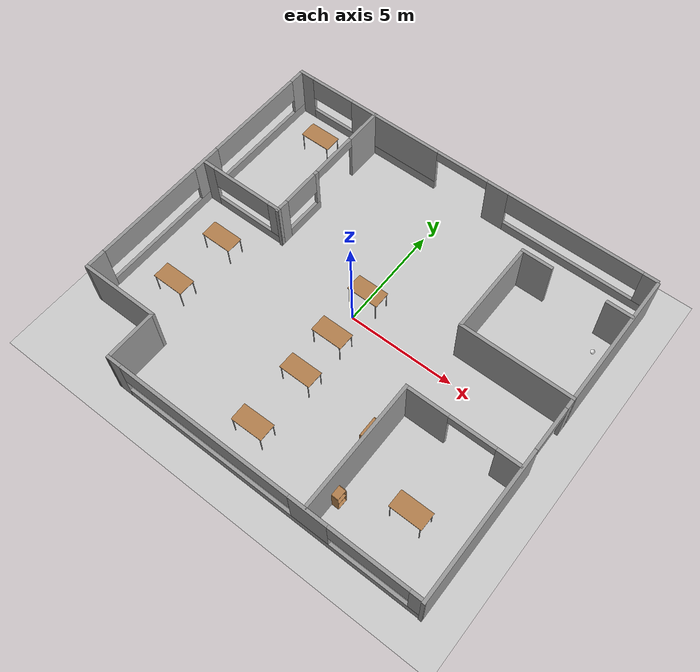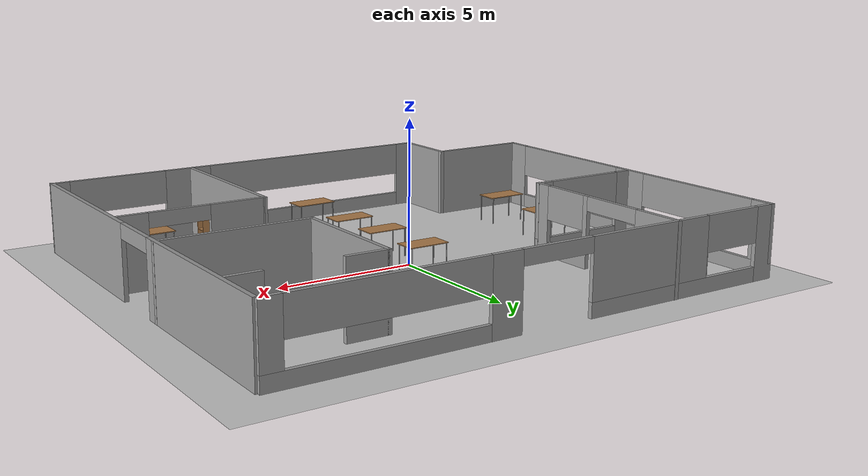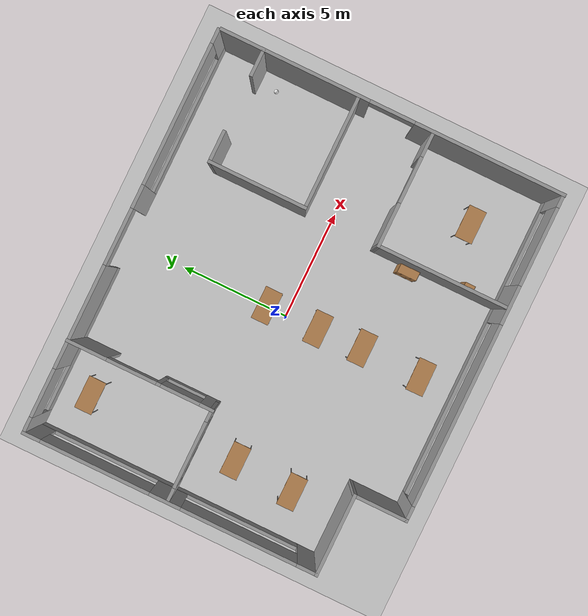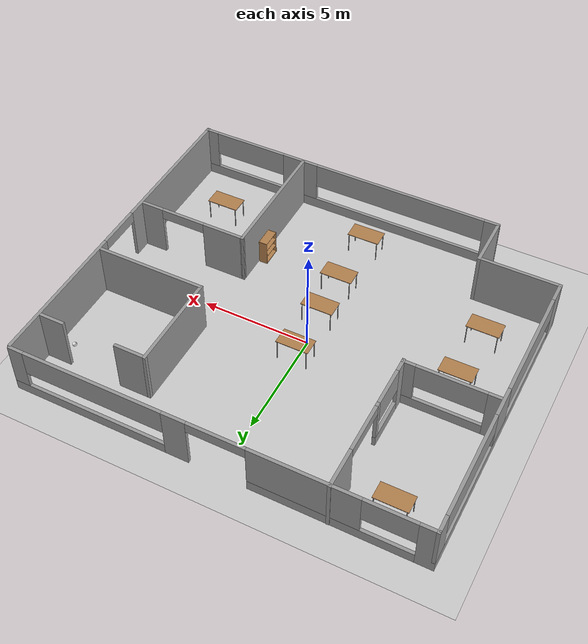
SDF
<sdf version="1.6">
 <world name="default">
  <plugin name="hello" filename="libhello.so"/>
  <light name="sun" type="directional">
   <pose>0 0 10 0 -0 0</pose>
   <diffuse>0.8 0.8 0.8 1</diffuse>
   <specular>0.2 0.2 0.2 1</specular>
   <attenuation>
    <range>1000</range>
    <constant>0.9</constant>
    <linear>0.01</linear>
    <quadratic>0.001</quadratic>
   </attenuation>
   <direction>-0.5 0.1 -0.9</direction>
  </light>
  <model name="ground_plane">
   <static>1</static>
   <link name="link">
    <collision name="collision">
     <geometry><plane><normal>0 0 1</normal><size>100 100</size></plane></geometry>
     <surface>
      <contact><collide_bitmask>65535</collide_bitmask></contact>
      <friction><ode><mu>100</mu><mu2>50</mu2></ode></friction>
     </surface>
    </collision>
    <visual name="visual">
     <cast_shadows>0</cast_shadows>
     <geometry><plane><normal>0 0 1</normal><size>100 100</size></plane></geometry>
     <material>
      <script><uri>file://media/materials/scripts/gazebo.material</uri><name>Gazebo/Grey</name></script>
     </material>
    </visual>
   </link>
  </model>
  <gravity>0 0 -9.8</gravity>
  <magnetic_field>6e-06 2.3e-05 -4.2e-05</magnetic_field>
  <atmosphere type="adiabatic"/>
  <physics name="default_physics" default="0" type="ode">
   <max_step_size>0.001</max_step_size>
   <real_time_factor>1</real_time_factor>
   <real_time_update_rate>1000</real_time_update_rate>
  </physics>
  <scene><ambient>0.4 0.4 0.4 1</ambient><background>0.7 0.7 0.7 1</background><shadows>1</shadows></scene>
  <spherical_coordinates>
   <surface_model>EARTH_WGS84</surface_model>
   <latitude_deg>0</latitude_deg>
   <longitude_deg>0</longitude_deg>
   <elevation>0</elevation>
   <heading_deg>0</heading_deg>
  </spherical_coordinates>
  <model name="my_office">
   <link name="Wall_0">
    <pose>1.79825 -7.84466 0 0 -0 0.001173</pose>
    <visual name="Wall_0_Visual_5">
     <pose>5.04846 0 1.9 0 -0 0</pose>
     <geometry><box><size>3.55344 0.15 1.2</size></box></geometry>
     <material>
      <script><uri>file://media/materials/scripts/gazebo.material</uri><name>Gazebo/Grey</name></script>
      <ambient>1 1 1 1</ambient>
      <shader type="pixel"/>
      <diffuse>0.7 0.7 0.7 1</diffuse>
      <specular>0.01 0.01 0.01 1</specular>
      <emissive>0 0 0 1</emissive>
     </material>
     <meta><layer>0</layer></meta>
    </visual>
    <visual name="Wall_0_Visual_1">
     <pose>0.362663 0 0.25 0 -0 0</pose>
     <geometry><box><size>14.2481 0.15 0.5</size></box></geometry>
     <material>
      <script><uri>file://media/materials/scripts/gazebo.material</uri><name>Gazebo/Grey</name></script>
      <ambient>1 1 1 1</ambient>
      <shader type="pixel"/>
      <diffuse>0.7 0.7 0.7 1</diffuse>
      <specular>0.01 0.01 0.01 1</specular>
      <emissive>0 0 0 1</emissive>
     </material>
     <meta><layer>0</layer></meta>
    </visual>
    <visual name="Wall_0_Visual_4">
     <pose>-2.62937 0 1.9 0 -0 0</pose>
     <geometry><box><size>8.26401 0.15 1.2</size></box></geometry>
     <material>
      <script><uri>file://media/materials/scripts/gazebo.material</uri><name>Gazebo/Grey</name></script>
      <ambient>1 1 1 1</ambient>
      <shader type="pixel"/>
      <diffuse>0.7 0.7 0.7 1</diffuse>
      <specular>0.01 0.01 0.01 1</specular>
      <emissive>0 0 0 1</emissive>
     </material>
     <meta><layer>0</layer></meta>
    </visual>
    <visual name="Wall_0_Visual_3">
     <pose>7.15595 0 1.5 0 -0 0</pose>
     <geometry><box><size>0.66152 0.15 2</size></box></geometry>
     <material>
      <script><uri>file://media/materials/scripts/gazebo.material</uri><name>Gazebo/Grey</name></script>
      <ambient>1 1 1 1</ambient>
      <shader type="pixel"/>
      <diffuse>0.7 0.7 0.7 1</diffuse>
      <specular>0.01 0.01 0.01 1</specular>
      <emissive>0 0 0 1</emissive>
     </material>
     <meta><layer>0</layer></meta>
    </visual>
    <visual name="Wall_0_Visual_0">
     <pose>-7.12404 0 1.25 0 -0 0</pose>
     <geometry><box><size>0.725327 0.15 2.5</size></box></geometry>
     <material>
      <script><uri>file://media/materials/scripts/gazebo.material</uri><name>Gazebo/Grey</name></script>
      <ambient>1 1 1 1</ambient>
      <shader type="pixel"/>
      <diffuse>0.7 0.7 0.7 1</diffuse>
      <specular>0.01 0.01 0.01 1</specular>
      <emissive>0 0 0 1</emissive>
     </material>
     <meta><layer>0</layer></meta>
    </visual>
    <visual name="Wall_0_Visual_2">
     <pose>2.38719 0 1.5 0 -0 0</pose>
     <geometry><box><size>1.76911 0.15 2</size></box></geometry>
     <material>
      <script><uri>file://media/materials/scripts/gazebo.material</uri><name>Gazebo/Grey</name></script>
      <ambient>1 1 1 1</ambient>
      <shader type="pixel"/>
      <diffuse>0.7 0.7 0.7 1</diffuse>
      <specular>0.01 0.01 0.01 1</specular>
      <emissive>0 0 0 1</emissive>
     </material>
     <meta><layer>0</layer></meta>
    </visual>
    <collision name="Wall_0_Collision_2">
     <pose>2.38719 0 1.5 0 -0 0</pose>
     <geometry><box><size>1.76911 0.15 2</size></box></geometry>
     <surface>
      <friction>
       <ode><mu>1</mu><mu2>1</mu2><fdir1>0 0 0</fdir1><slip1>0</slip1><slip2>0</slip2></ode>
       <torsional>
        <coefficient>1</coefficient>
        <patch_radius>0</patch_radius>
        <surface_radius>0</surface_radius>
        <use_patch_radius>1</use_patch_radius>
        <ode><slip>0</slip></ode>
       </torsional>
      </friction>
      <bounce><restitution_coefficient>0</restitution_coefficient><threshold>1e+06</threshold></bounce>
      <contact>
       <collide_without_contact>0</collide_without_contact>
       <collide_without_contact_bitmask>1</collide_without_contact_bitmask>
       <collide_bitmask>1</collide_bitmask>
       <ode>
        <soft_cfm>0</soft_cfm>
        <soft_erp>0.2</soft_erp>
        <kp>1e+13</kp>
        <kd>1</kd>
        <max_vel>0.01</max_vel>
        <min_depth>0</min_depth>
       </ode>
       <bullet>
        <split_impulse>1</split_impulse>
        <split_impulse_penetration_threshold>-0.01</split_impulse_penetration_threshold>
        <soft_cfm>0</soft_cfm>
        <soft_erp>0.2</soft_erp>
        <kp>1e+13</kp>
        <kd>1</kd>
       </bullet>
      </contact>
     </surface>
    </collision>
    <collision name="Wall_0_Collision_3">
     <pose>7.15595 0 1.5 0 -0 0</pose>
     <geometry><box><size>0.66152 0.15 2</size></box></geometry>
     <surface>
      <friction>
       <ode><mu>1</mu><mu2>1</mu2><fdir1>0 0 0</fdir1><slip1>0</slip1><slip2>0</slip2></ode>
       <torsional>
        <coefficient>1</coefficient>
        <patch_radius>0</patch_radius>
        <surface_radius>0</surface_radius>
        <use_patch_radius>1</use_patch_radius>
        <ode><slip>0</slip></ode>
       </torsional>
      </friction>
      <bounce><restitution_coefficient>0</restitution_coefficient><threshold>1e+06</threshold></bounce>
      <contact>
       <collide_without_contact>0</collide_without_contact>
       <collide_without_contact_bitmask>1</collide_without_contact_bitmask>
       <collide_bitmask>1</collide_bitmask>
       <ode>
        <soft_cfm>0</soft_cfm>
        <soft_erp>0.2</soft_erp>
        <kp>1e+13</kp>
        <kd>1</kd>
        <max_vel>0.01</max_vel>
        <min_depth>0</min_depth>
       </ode>
       <bullet>
        <split_impulse>1</split_impulse>
        <split_impulse_penetration_threshold>-0.01</split_impulse_penetration_threshold>
        <soft_cfm>0</soft_cfm>
        <soft_erp>0.2</soft_erp>
        <kp>1e+13</kp>
        <kd>1</kd>
       </bullet>
      </contact>
     </surface>
    </collision>
    <collision name="Wall_0_Collision_0">
     <pose>-7.12404 0 1.25 0 -0 0</pose>
     <geometry><box><size>0.725327 0.15 2.5</size></box></geometry>
     <surface>
      <friction>
       <ode><mu>1</mu><mu2>1</mu2><fdir1>0 0 0</fdir1><slip1>0</slip1><slip2>0</slip2></ode>
       <torsional>
        <coefficient>1</coefficient>
        <patch_radius>0</patch_radius>
        <surface_radius>0</surface_radius>
        <use_patch_radius>1</use_patch_radius>
        <ode><slip>0</slip></ode>
       </torsional>
      </friction>
      <bounce><restitution_coefficient>0</restitution_coefficient><threshold>1e+06</threshold></bounce>
      <contact>
       <collide_without_contact>0</collide_without_contact>
       <collide_without_contact_bitmask>1</collide_without_contact_bitmask>
       <collide_bitmask>1</collide_bitmask>
       <ode>
        <soft_cfm>0</soft_cfm>
        <soft_erp>0.2</soft_erp>
        <kp>1e+13</kp>
        <kd>1</kd>
        <max_vel>0.01</max_vel>
        <min_depth>0</min_depth>
       </ode>
       <bullet>
        <split_impulse>1</split_impulse>
        <split_impulse_penetration_threshold>-0.01</split_impulse_penetration_threshold>
        <soft_cfm>0</soft_cfm>
        <soft_erp>0.2</soft_erp>
        <kp>1e+13</kp>
        <kd>1</kd>
       </bullet>
      </contact>
     </surface>
    </collision>
    <collision name="Wall_0_Collision_1">
     <pose>0.362663 0 0.25 0 -0 0</pose>
     <geometry><box><size>14.2481 0.15 0.5</size></box></geometry>
     <surface>
      <friction>
       <ode><mu>1</mu><mu2>1</mu2><fdir1>0 0 0</fdir1><slip1>0</slip1><slip2>0</slip2></ode>
       <torsional>
        <coefficient>1</coefficient>
        <patch_radius>0</patch_radius>
        <surface_radius>0</surface_radius>
        <use_patch_radius>1</use_patch_radius>
        <ode><slip>0</slip></ode>
       </torsional>
      </friction>
      <bounce><restitution_coefficient>0</restitution_coefficient><threshold>1e+06</threshold></bounce>
      <contact>
       <collide_without_contact>0</collide_without_contact>
       <collide_without_contact_bitmask>1</collide_without_contact_bitmask>
       <collide_bitmask>1</collide_bitmask>
       <ode>
        <soft_cfm>0</soft_cfm>
        <soft_erp>0.2</soft_erp>
        <kp>1e+13</kp>
        <kd>1</kd>
        <max_vel>0.01</max_vel>
        <min_depth>0</min_depth>
       </ode>
       <bullet>
        <split_impulse>1</split_impulse>
        <split_impulse_penetration_threshold>-0.01</split_impulse_penetration_threshold>
        <soft_cfm>0</soft_cfm>
        <soft_erp>0.2</soft_erp>
        <kp>1e+13</kp>
        <kd>1</kd>
       </bullet>
      </contact>
     </surface>
    </collision>
    <collision name="Wall_0_Collision_4">
     <pose>-2.62937 0 1.9 0 -0 0</pose>
     <geometry><box><size>8.26401 0.15 1.2</size></box></geometry>
     <surface>
      <friction>
       <ode><mu>1</mu><mu2>1</mu2><fdir1>0 0 0</fdir1><slip1>0</slip1><slip2>0</slip2></ode>
       <torsional>
        <coefficient>1</coefficient>
        <patch_radius>0</patch_radius>
        <surface_radius>0</surface_radius>
        <use_patch_radius>1</use_patch_radius>
        <ode><slip>0</slip></ode>
       </torsional>
      </friction>
      <bounce><restitution_coefficient>0</restitution_coefficient><threshold>1e+06</threshold></bounce>
      <contact>
       <collide_without_contact>0</collide_without_contact>
       <collide_without_contact_bitmask>1</collide_without_contact_bitmask>
       <collide_bitmask>1</collide_bitmask>
       <ode>
        <soft_cfm>0</soft_cfm>
        <soft_erp>0.2</soft_erp>
        <kp>1e+13</kp>
        <kd>1</kd>
        <max_vel>0.01</max_vel>
        <min_depth>0</min_depth>
       </ode>
       <bullet>
        <split_impulse>1</split_impulse>
        <split_impulse_penetration_threshold>-0.01</split_impulse_penetration_threshold>
        <soft_cfm>0</soft_cfm>
        <soft_erp>0.2</soft_erp>
        <kp>1e+13</kp>
        <kd>1</kd>
       </bullet>
      </contact>
     </surface>
    </collision>
    <collision name="Wall_0_Collision_5">
     <pose>5.04846 0 1.9 0 -0 0</pose>
     <geometry><box><size>3.55344 0.15 1.2</size></box></geometry>
     <surface>
      <friction>
       <ode><mu>1</mu><mu2>1</mu2><fdir1>0 0 0</fdir1><slip1>0</slip1><slip2>0</slip2></ode>
       <torsional>
        <coefficient>1</coefficient>
        <patch_radius>0</patch_radius>
        <surface_radius>0</surface_radius>
        <use_patch_radius>1</use_patch_radius>
        <ode><slip>0</slip></ode>
       </torsional>
      </friction>
      <bounce><restitution_coefficient>0</restitution_coefficient><threshold>1e+06</threshold></bounce>
      <contact>
       <collide_without_contact>0</collide_without_contact>
       <collide_without_contact_bitmask>1</collide_without_contact_bitmask>
       <collide_bitmask>1</collide_bitmask>
       <ode>
        <soft_cfm>0</soft_cfm>
        <soft_erp>0.2</soft_erp>
        <kp>1e+13</kp>
        <kd>1</kd>
        <max_vel>0.01</max_vel>
        <min_depth>0</min_depth>
       </ode>
       <bullet>
        <split_impulse>1</split_impulse>
        <split_impulse_penetration_threshold>-0.01</split_impulse_penetration_threshold>
        <soft_cfm>0</soft_cfm>
        <soft_erp>0.2</soft_erp>
        <kp>1e+13</kp>
        <kd>1</kd>
       </bullet>
      </contact>
     </surface>
    </collision>
   </link>
   <link name="Wall_2">
    <pose>6.57555 -1.92036 0 0 -0 3.14159</pose>
    <visual name="Wall_2_Visual_2">
     <pose>-0.453224 0 2.25 0 -0 0</pose>
     <geometry><box><size>2.1 0.15 0.5</size></box></geometry>
     <material>
      <script><uri>file://media/materials/scripts/gazebo.material</uri><name>Gazebo/Grey</name></script>
      <ambient>1 1 1 1</ambient>
      <shader type="pixel"/>
      <diffuse>0.7 0.7 0.7 1</diffuse>
      <specular>0.01 0.01 0.01 1</specular>
      <emissive>0 0 0 1</emissive>
     </material>
     <meta><layer>0</layer></meta>
    </visual>
    <visual name="Wall_2_Visual_1">
     <pose>1.61089 0 1.25 0 -0 0</pose>
     <geometry><box><size>2.02822 0.15 2.5</size></box></geometry>
     <material>
      <script><uri>file://media/materials/scripts/gazebo.material</uri><name>Gazebo/Grey</name></script>
      <ambient>1 1 1 1</ambient>
      <shader type="pixel"/>
      <diffuse>0.7 0.7 0.7 1</diffuse>
      <specular>0.01 0.01 0.01 1</specular>
      <emissive>0 0 0 1</emissive>
     </material>
     <meta><layer>0</layer></meta>
    </visual>
    <visual name="Wall_2_Visual_0">
     <pose>-2.06411 0 1.25 0 -0 0</pose>
     <geometry><box><size>1.12178 0.15 2.5</size></box></geometry>
     <material>
      <script><uri>file://media/materials/scripts/gazebo.material</uri><name>Gazebo/Grey</name></script>
      <ambient>1 1 1 1</ambient>
      <shader type="pixel"/>
      <diffuse>0.7 0.7 0.7 1</diffuse>
      <specular>0.01 0.01 0.01 1</specular>
      <emissive>0 0 0 1</emissive>
     </material>
     <meta><layer>0</layer></meta>
    </visual>
    <collision name="Wall_2_Collision_1">
     <pose>1.61089 0 1.25 0 -0 0</pose>
     <geometry><box><size>2.02822 0.15 2.5</size></box></geometry>
     <surface>
      <friction>
       <ode><mu>1</mu><mu2>1</mu2><fdir1>0 0 0</fdir1><slip1>0</slip1><slip2>0</slip2></ode>
       <torsional>
        <coefficient>1</coefficient>
        <patch_radius>0</patch_radius>
        <surface_radius>0</surface_radius>
        <use_patch_radius>1</use_patch_radius>
        <ode><slip>0</slip></ode>
       </torsional>
      </friction>
      <bounce><restitution_coefficient>0</restitution_coefficient><threshold>1e+06</threshold></bounce>
      <contact>
       <collide_without_contact>0</collide_without_contact>
       <collide_without_contact_bitmask>1</collide_without_contact_bitmask>
       <collide_bitmask>1</collide_bitmask>
       <ode>
        <soft_cfm>0</soft_cfm>
        <soft_erp>0.2</soft_erp>
        <kp>1e+13</kp>
        <kd>1</kd>
        <max_vel>0.01</max_vel>
        <min_depth>0</min_depth>
       </ode>
       <bullet>
        <split_impulse>1</split_impulse>
        <split_impulse_penetration_threshold>-0.01</split_impulse_penetration_threshold>
        <soft_cfm>0</soft_cfm>
        <soft_erp>0.2</soft_erp>
        <kp>1e+13</kp>
        <kd>1</kd>
       </bullet>
      </contact>
     </surface>
    </collision>
    <collision name="Wall_2_Collision_0">
     <pose>-2.06411 0 1.25 0 -0 0</pose>
     <geometry><box><size>1.12178 0.15 2.5</size></box></geometry>
     <surface>
      <friction>
       <ode><mu>1</mu><mu2>1</mu2><fdir1>0 0 0</fdir1><slip1>0</slip1><slip2>0</slip2></ode>
       <torsional>
        <coefficient>1</coefficient>
        <patch_radius>0</patch_radius>
        <surface_radius>0</surface_radius>
        <use_patch_radius>1</use_patch_radius>
        <ode><slip>0</slip></ode>
       </torsional>
      </friction>
      <bounce><restitution_coefficient>0</restitution_coefficient><threshold>1e+06</threshold></bounce>
      <contact>
       <collide_without_contact>0</collide_without_contact>
       <collide_without_contact_bitmask>1</collide_without_contact_bitmask>
       <collide_bitmask>1</collide_bitmask>
       <ode>
        <soft_cfm>0</soft_cfm>
        <soft_erp>0.2</soft_erp>
        <kp>1e+13</kp>
        <kd>1</kd>
        <max_vel>0.01</max_vel>
        <min_depth>0</min_depth>
       </ode>
       <bullet>
        <split_impulse>1</split_impulse>
        <split_impulse_penetration_threshold>-0.01</split_impulse_penetration_threshold>
        <soft_cfm>0</soft_cfm>
        <soft_erp>0.2</soft_erp>
        <kp>1e+13</kp>
        <kd>1</kd>
       </bullet>
      </contact>
     </surface>
    </collision>
    <collision name="Wall_2_Collision_2">
     <pose>-0.453224 0 2.25 0 -0 0</pose>
     <geometry><box><size>2.1 0.15 0.5</size></box></geometry>
     <surface>
      <friction>
       <ode><mu>1</mu><mu2>1</mu2><fdir1>0 0 0</fdir1><slip1>0</slip1><slip2>0</slip2></ode>
       <torsional>
        <coefficient>1</coefficient>
        <patch_radius>0</patch_radius>
        <surface_radius>0</surface_radius>
        <use_patch_radius>1</use_patch_radius>
        <ode><slip>0</slip></ode>
       </torsional>
      </friction>
      <bounce><restitution_coefficient>0</restitution_coefficient><threshold>1e+06</threshold></bounce>
      <contact>
       <collide_without_contact>0</collide_without_contact>
       <collide_without_contact_bitmask>1</collide_without_contact_bitmask>
       <collide_bitmask>1</collide_bitmask>
       <ode>
        <soft_cfm>0</soft_cfm>
        <soft_erp>0.2</soft_erp>
        <kp>1e+13</kp>
        <kd>1</kd>
        <max_vel>0.01</max_vel>
        <min_depth>0</min_depth>
       </ode>
       <bullet>
        <split_impulse>1</split_impulse>
        <split_impulse_penetration_threshold>-0.01</split_impulse_penetration_threshold>
        <soft_cfm>0</soft_cfm>
        <soft_erp>0.2</soft_erp>
        <kp>1e+13</kp>
        <kd>1</kd>
       </bullet>
      </contact>
     </surface>
    </collision>
   </link>
   <link name="Wall_24">
    <pose>9.20995 -0.062568 0 0 -0 1.5708</pose>
    <visual name="Wall_24_Visual_0">
     <pose>-4.43928 0 1.25 0 -0 0</pose>
     <geometry><box><size>6.87144 0.15 2.5</size></box></geometry>
     <material>
      <script><uri>file://media/materials/scripts/gazebo.material</uri><name>Gazebo/Grey</name></script>
      <ambient>1 1 1 1</ambient>
      <shader type="pixel"/>
      <diffuse>0.7 0.7 0.7 1</diffuse>
      <specular>0.01 0.01 0.01 1</specular>
      <emissive>0 0 0 1</emissive>
     </material>
     <meta><layer>0</layer></meta>
    </visual>
    <visual name="Wall_24_Visual_1">
     <pose>4.45763 0 1.25 0 -0 0</pose>
     <geometry><box><size>6.83475 0.15 2.5</size></box></geometry>
     <material>
      <script><uri>file://media/materials/scripts/gazebo.material</uri><name>Gazebo/Grey</name></script>
      <ambient>1 1 1 1</ambient>
      <shader type="pixel"/>
      <diffuse>0.7 0.7 0.7 1</diffuse>
      <specular>0.01 0.01 0.01 1</specular>
      <emissive>0 0 0 1</emissive>
     </material>
     <meta><layer>0</layer></meta>
    </visual>
    <visual name="Wall_24_Visual_2">
     <pose>0.018345 0 2.25 0 -0 0</pose>
     <geometry><box><size>2.04381 0.15 0.5</size></box></geometry>
     <material>
      <script><uri>file://media/materials/scripts/gazebo.material</uri><name>Gazebo/Grey</name></script>
      <ambient>1 1 1 1</ambient>
      <shader type="pixel"/>
      <diffuse>0.7 0.7 0.7 1</diffuse>
      <specular>0.01 0.01 0.01 1</specular>
      <emissive>0 0 0 1</emissive>
     </material>
     <meta><layer>0</layer></meta>
    </visual>
    <collision name="Wall_24_Collision_1">
     <pose>4.45763 0 1.25 0 -0 0</pose>
     <geometry><box><size>6.83475 0.15 2.5</size></box></geometry>
     <surface>
      <friction>
       <ode><mu>1</mu><mu2>1</mu2><fdir1>0 0 0</fdir1><slip1>0</slip1><slip2>0</slip2></ode>
       <torsional>
        <coefficient>1</coefficient>
        <patch_radius>0</patch_radius>
        <surface_radius>0</surface_radius>
        <use_patch_radius>1</use_patch_radius>
        <ode><slip>0</slip></ode>
       </torsional>
      </friction>
      <bounce><restitution_coefficient>0</restitution_coefficient><threshold>1e+06</threshold></bounce>
      <contact>
       <collide_without_contact>0</collide_without_contact>
       <collide_without_contact_bitmask>1</collide_without_contact_bitmask>
       <collide_bitmask>1</collide_bitmask>
       <ode>
        <soft_cfm>0</soft_cfm>
        <soft_erp>0.2</soft_erp>
        <kp>1e+13</kp>
        <kd>1</kd>
        <max_vel>0.01</max_vel>
        <min_depth>0</min_depth>
       </ode>
       <bullet>
        <split_impulse>1</split_impulse>
        <split_impulse_penetration_threshold>-0.01</split_impulse_penetration_threshold>
        <soft_cfm>0</soft_cfm>
        <soft_erp>0.2</soft_erp>
        <kp>1e+13</kp>
        <kd>1</kd>
       </bullet>
      </contact>
     </surface>
    </collision>
    <collision name="Wall_24_Collision_0">
     <pose>-4.43928 0 1.25 0 -0 0</pose>
     <geometry><box><size>6.87144 0.15 2.5</size></box></geometry>
     <surface>
      <friction>
       <ode><mu>1</mu><mu2>1</mu2><fdir1>0 0 0</fdir1><slip1>0</slip1><slip2>0</slip2></ode>
       <torsional>
        <coefficient>1</coefficient>
        <patch_radius>0</patch_radius>
        <surface_radius>0</surface_radius>
        <use_patch_radius>1</use_patch_radius>
        <ode><slip>0</slip></ode>
       </torsional>
      </friction>
      <bounce><restitution_coefficient>0</restitution_coefficient><threshold>1e+06</threshold></bounce>
      <contact>
       <collide_without_contact>0</collide_without_contact>
       <collide_without_contact_bitmask>1</collide_without_contact_bitmask>
       <collide_bitmask>1</collide_bitmask>
       <ode>
        <soft_cfm>0</soft_cfm>
        <soft_erp>0.2</soft_erp>
        <kp>1e+13</kp>
        <kd>1</kd>
        <max_vel>0.01</max_vel>
        <min_depth>0</min_depth>
       </ode>
       <bullet>
        <split_impulse>1</split_impulse>
        <split_impulse_penetration_threshold>-0.01</split_impulse_penetration_threshold>
        <soft_cfm>0</soft_cfm>
        <soft_erp>0.2</soft_erp>
        <kp>1e+13</kp>
        <kd>1</kd>
       </bullet>
      </contact>
     </surface>
    </collision>
    <collision name="Wall_24_Collision_2">
     <pose>0.018345 0 2.25 0 -0 0</pose>
     <geometry><box><size>2.04381 0.15 0.5</size></box></geometry>
     <surface>
      <friction>
       <ode><mu>1</mu><mu2>1</mu2><fdir1>0 0 0</fdir1><slip1>0</slip1><slip2>0</slip2></ode>
       <torsional>
        <coefficient>1</coefficient>
        <patch_radius>0</patch_radius>
        <surface_radius>0</surface_radius>
        <use_patch_radius>1</use_patch_radius>
        <ode><slip>0</slip></ode>
       </torsional>
      </friction>
      <bounce><restitution_coefficient>0</restitution_coefficient><threshold>1e+06</threshold></bounce>
      <contact>
       <collide_without_contact>0</collide_without_contact>
       <collide_without_contact_bitmask>1</collide_without_contact_bitmask>
       <collide_bitmask>1</collide_bitmask>
       <ode>
        <soft_cfm>0</soft_cfm>
        <soft_erp>0.2</soft_erp>
        <kp>1e+13</kp>
        <kd>1</kd>
        <max_vel>0.01</max_vel>
        <min_depth>0</min_depth>
       </ode>
       <bullet>
        <split_impulse>1</split_impulse>
        <split_impulse_penetration_threshold>-0.01</split_impulse_penetration_threshold>
        <soft_cfm>0</soft_cfm>
        <soft_erp>0.2</soft_erp>
        <kp>1e+13</kp>
        <kd>1</kd>
       </bullet>
      </contact>
     </surface>
    </collision>
   </link>
   <link name="Wall_3">
    <pose>4.03125 -4.84539 0 0 0 -1.56885</pose>
    <visual name="Wall_3_Visual">
     <pose>0 0 1.25 0 -0 0</pose>
     <geometry><box><size>6 0.15 2.5</size></box></geometry>
     <material>
      <script><uri>file://media/materials/scripts/gazebo.material</uri><name>Gazebo/Grey</name></script>
      <ambient>1 1 1 1</ambient>
      <shader type="pixel"/>
      <diffuse>0.7 0.7 0.7 1</diffuse>
      <specular>0.01 0.01 0.01 1</specular>
      <emissive>0 0 0 1</emissive>
     </material>
     <meta><layer>0</layer></meta>
    </visual>
    <collision name="Wall_3_Collision">
     <pose>0 0 1.25 0 -0 0</pose>
     <geometry><box><size>6 0.15 2.5</size></box></geometry>
     <surface>
      <friction>
       <ode><mu>1</mu><mu2>1</mu2><fdir1>0 0 0</fdir1><slip1>0</slip1><slip2>0</slip2></ode>
       <torsional>
        <coefficient>1</coefficient>
        <patch_radius>0</patch_radius>
        <surface_radius>0</surface_radius>
        <use_patch_radius>1</use_patch_radius>
        <ode><slip>0</slip></ode>
       </torsional>
      </friction>
      <bounce><restitution_coefficient>0</restitution_coefficient><threshold>1e+06</threshold></bounce>
      <contact>
       <collide_without_contact>0</collide_without_contact>
       <collide_without_contact_bitmask>1</collide_without_contact_bitmask>
       <collide_bitmask>1</collide_bitmask>
       <ode>
        <soft_cfm>0</soft_cfm>
        <soft_erp>0.2</soft_erp>
        <kp>1e+13</kp>
        <kd>1</kd>
        <max_vel>0.01</max_vel>
        <min_depth>0</min_depth>
       </ode>
       <bullet>
        <split_impulse>1</split_impulse>
        <split_impulse_penetration_threshold>-0.01</split_impulse_penetration_threshold>
        <soft_cfm>0</soft_cfm>
        <soft_erp>0.2</soft_erp>
        <kp>1e+13</kp>
        <kd>1</kd>
       </bullet>
      </contact>
     </surface>
    </collision>
   </link>
   <link name="Wall_33">
    <pose>4.11345 3.64668 0 0 0 -1.5708</pose>
    <visual name="Wall_33_Visual">
     <pose>0 0 1.25 0 -0 0</pose>
     <geometry><box><size>4.5 0.15 2.5</size></box></geometry>
     <material>
      <script><uri>file://media/materials/scripts/gazebo.material</uri><name>Gazebo/Grey</name></script>
      <ambient>1 1 1 1</ambient>
      <shader type="pixel"/>
      <diffuse>0.7 0.7 0.7 1</diffuse>
      <specular>0.01 0.01 0.01 1</specular>
      <emissive>0 0 0 1</emissive>
     </material>
     <meta><layer>0</layer></meta>
    </visual>
    <collision name="Wall_33_Collision">
     <pose>0 0 1.25 0 -0 0</pose>
     <geometry><box><size>4.5 0.15 2.5</size></box></geometry>
     <surface>
      <friction>
       <ode><mu>1</mu><mu2>1</mu2><fdir1>0 0 0</fdir1><slip1>0</slip1><slip2>0</slip2></ode>
       <torsional>
        <coefficient>1</coefficient>
        <patch_radius>0</patch_radius>
        <surface_radius>0</surface_radius>
        <use_patch_radius>1</use_patch_radius>
        <ode><slip>0</slip></ode>
       </torsional>
      </friction>
      <bounce><restitution_coefficient>0</restitution_coefficient><threshold>1e+06</threshold></bounce>
      <contact>
       <collide_without_contact>0</collide_without_contact>
       <collide_without_contact_bitmask>1</collide_without_contact_bitmask>
       <collide_bitmask>1</collide_bitmask>
       <ode>
        <soft_cfm>0</soft_cfm>
        <soft_erp>0.2</soft_erp>
        <kp>1e+13</kp>
        <kd>1</kd>
        <max_vel>0.01</max_vel>
        <min_depth>0</min_depth>
       </ode>
       <bullet>
        <split_impulse>1</split_impulse>
        <split_impulse_penetration_threshold>-0.01</split_impulse_penetration_threshold>
        <soft_cfm>0</soft_cfm>
        <soft_erp>0.2</soft_erp>
        <kp>1e+13</kp>
        <kd>1</kd>
       </bullet>
      </contact>
     </surface>
    </collision>
   </link>
   <link name="Wall_34">
    <pose>6.66345 1.47168 0 0 -0 0</pose>
    <visual name="Wall_34_Visual">
     <pose>0 0 1.25 0 -0 0</pose>
     <geometry><box><size>5.25 0.15 2.5</size></box></geometry>
     <material>
      <script><uri>file://media/materials/scripts/gazebo.material</uri><name>Gazebo/Grey</name></script>
      <ambient>1 1 1 1</ambient>
      <shader type="pixel"/>
      <diffuse>0.7 0.7 0.7 1</diffuse>
      <specular>0.01 0.01 0.01 1</specular>
      <emissive>0 0 0 1</emissive>
     </material>
     <meta><layer>0</layer></meta>
    </visual>
    <collision name="Wall_34_Collision">
     <pose>0 0 1.25 0 -0 0</pose>
     <geometry><box><size>5.25 0.15 2.5</size></box></geometry>
     <surface>
      <friction>
       <ode><mu>1</mu><mu2>1</mu2><fdir1>0 0 0</fdir1><slip1>0</slip1><slip2>0</slip2></ode>
       <torsional>
        <coefficient>1</coefficient>
        <patch_radius>0</patch_radius>
        <surface_radius>0</surface_radius>
        <use_patch_radius>1</use_patch_radius>
        <ode><slip>0</slip></ode>
       </torsional>
      </friction>
      <bounce><restitution_coefficient>0</restitution_coefficient><threshold>1e+06</threshold></bounce>
      <contact>
       <collide_without_contact>0</collide_without_contact>
       <collide_without_contact_bitmask>1</collide_without_contact_bitmask>
       <collide_bitmask>1</collide_bitmask>
       <ode>
        <soft_cfm>0</soft_cfm>
        <soft_erp>0.2</soft_erp>
        <kp>1e+13</kp>
        <kd>1</kd>
        <max_vel>0.01</max_vel>
        <min_depth>0</min_depth>
       </ode>
       <bullet>
        <split_impulse>1</split_impulse>
        <split_impulse_penetration_threshold>-0.01</split_impulse_penetration_threshold>
        <soft_cfm>0</soft_cfm>
        <soft_erp>0.2</soft_erp>
        <kp>1e+13</kp>
        <kd>1</kd>
       </bullet>
      </contact>
     </surface>
    </collision>
   </link>
   <link name="Wall_41">
    <pose>4.78845 5.82168 0 0 -0 0</pose>
    <visual name="Wall_41_Visual">
     <pose>0 0 1.25 0 -0 0</pose>
     <geometry><box><size>1.5 0.15 2.5</size></box></geometry>
     <material>
      <script><uri>file://media/materials/scripts/gazebo.material</uri><name>Gazebo/Grey</name></script>
      <ambient>1 1 1 1</ambient>
      <shader type="pixel"/>
      <diffuse>0.7 0.7 0.7 1</diffuse>
      <specular>0.01 0.01 0.01 1</specular>
      <emissive>0 0 0 1</emissive>
     </material>
     <meta><layer>0</layer></meta>
    </visual>
    <collision name="Wall_41_Collision">
     <pose>0 0 1.25 0 -0 0</pose>
     <geometry><box><size>1.5 0.15 2.5</size></box></geometry>
     <surface>
      <friction>
       <ode><mu>1</mu><mu2>1</mu2><fdir1>0 0 0</fdir1><slip1>0</slip1><slip2>0</slip2></ode>
       <torsional>
        <coefficient>1</coefficient>
        <patch_radius>0</patch_radius>
        <surface_radius>0</surface_radius>
        <use_patch_radius>1</use_patch_radius>
        <ode><slip>0</slip></ode>
       </torsional>
      </friction>
      <bounce><restitution_coefficient>0</restitution_coefficient><threshold>1e+06</threshold></bounce>
      <contact>
       <collide_without_contact>0</collide_without_contact>
       <collide_without_contact_bitmask>1</collide_without_contact_bitmask>
       <collide_bitmask>1</collide_bitmask>
       <ode>
        <soft_cfm>0</soft_cfm>
        <soft_erp>0.2</soft_erp>
        <kp>1e+13</kp>
        <kd>1</kd>
        <max_vel>0.01</max_vel>
        <min_depth>0</min_depth>
       </ode>
       <bullet>
        <split_impulse>1</split_impulse>
        <split_impulse_penetration_threshold>-0.01</split_impulse_penetration_threshold>
        <soft_cfm>0</soft_cfm>
        <soft_erp>0.2</soft_erp>
        <kp>1e+13</kp>
        <kd>1</kd>
       </bullet>
      </contact>
     </surface>
    </collision>
   </link>
   <link name="Wall_43">
    <pose>8.61345 5.82168 0 0 -0 0</pose>
    <visual name="Wall_43_Visual">
     <pose>0 0 1.25 0 -0 0</pose>
     <geometry><box><size>1.25 0.15 2.5</size></box></geometry>
     <material>
      <script><uri>file://media/materials/scripts/gazebo.material</uri><name>Gazebo/Grey</name></script>
      <ambient>1 1 1 1</ambient>
      <shader type="pixel"/>
      <diffuse>0.7 0.7 0.7 1</diffuse>
      <specular>0.01 0.01 0.01 1</specular>
      <emissive>0 0 0 1</emissive>
     </material>
     <meta><layer>0</layer></meta>
    </visual>
    <collision name="Wall_43_Collision">
     <pose>0 0 1.25 0 -0 0</pose>
     <geometry><box><size>1.25 0.15 2.5</size></box></geometry>
     <surface>
      <friction>
       <ode><mu>1</mu><mu2>1</mu2><fdir1>0 0 0</fdir1><slip1>0</slip1><slip2>0</slip2></ode>
       <torsional>
        <coefficient>1</coefficient>
        <patch_radius>0</patch_radius>
        <surface_radius>0</surface_radius>
        <use_patch_radius>1</use_patch_radius>
        <ode><slip>0</slip></ode>
       </torsional>
      </friction>
      <bounce><restitution_coefficient>0</restitution_coefficient><threshold>1e+06</threshold></bounce>
      <contact>
       <collide_without_contact>0</collide_without_contact>
       <collide_without_contact_bitmask>1</collide_without_contact_bitmask>
       <collide_bitmask>1</collide_bitmask>
       <ode>
        <soft_cfm>0</soft_cfm>
        <soft_erp>0.2</soft_erp>
        <kp>1e+13</kp>
        <kd>1</kd>
        <max_vel>0.01</max_vel>
        <min_depth>0</min_depth>
       </ode>
       <bullet>
        <split_impulse>1</split_impulse>
        <split_impulse_penetration_threshold>-0.01</split_impulse_penetration_threshold>
        <soft_cfm>0</soft_cfm>
        <soft_erp>0.2</soft_erp>
        <kp>1e+13</kp>
        <kd>1</kd>
       </bullet>
      </contact>
     </surface>
    </collision>
   </link>
   <link name="Wall_46">
    <pose>-5.01478 4.56257 0 0 -0 1.5708</pose>
    <visual name="Wall_46_Visual_0">
     <pose>-3.04368 0 1.25 0 -0 0</pose>
     <geometry><box><size>0.662647 0.15 2.5</size></box></geometry>
     <material>
      <script><uri>file://media/materials/scripts/gazebo.material</uri><name>Gazebo/Grey</name></script>
      <ambient>1 1 1 1</ambient>
      <shader type="pixel"/>
      <diffuse>0.7 0.7 0.7 1</diffuse>
      <specular>0.01 0.01 0.01 1</specular>
      <emissive>0 0 0 1</emissive>
     </material>
     <meta><layer>0</layer></meta>
    </visual>
    <visual name="Wall_46_Visual_1">
     <pose>2.45072 0 1.25 0 -0 0</pose>
     <geometry><box><size>1.84856 0.15 2.5</size></box></geometry>
     <material>
      <script><uri>file://media/materials/scripts/gazebo.material</uri><name>Gazebo/Grey</name></script>
      <ambient>1 1 1 1</ambient>
      <shader type="pixel"/>
      <diffuse>0.7 0.7 0.7 1</diffuse>
      <specular>0.01 0.01 0.01 1</specular>
      <emissive>0 0 0 1</emissive>
     </material>
     <meta><layer>0</layer></meta>
    </visual>
    <visual name="Wall_46_Visual_2">
     <pose>-1.71975 0 0.25 0 -0 0</pose>
     <geometry><box><size>1.98521 0.15 0.5</size></box></geometry>
     <material>
      <script><uri>file://media/materials/scripts/gazebo.material</uri><name>Gazebo/Grey</name></script>
      <ambient>1 1 1 1</ambient>
      <shader type="pixel"/>
      <diffuse>0.7 0.7 0.7 1</diffuse>
      <specular>0.01 0.01 0.01 1</specular>
      <emissive>0 0 0 1</emissive>
     </material>
     <meta><layer>0</layer></meta>
    </visual>
    <visual name="Wall_46_Visual_3">
     <pose>-0.827243 0 1.5 0 -0 0</pose>
     <geometry><box><size>0.200209 0.15 2</size></box></geometry>
     <material>
      <script><uri>file://media/materials/scripts/gazebo.material</uri><name>Gazebo/Grey</name></script>
      <ambient>1 1 1 1</ambient>
      <shader type="pixel"/>
      <diffuse>0.7 0.7 0.7 1</diffuse>
      <specular>0.01 0.01 0.01 1</specular>
      <emissive>0 0 0 1</emissive>
     </material>
     <meta><layer>0</layer></meta>
    </visual>
    <visual name="Wall_46_Visual_4">
     <pose>-1.81985 0 1.9 0 -0 0</pose>
     <geometry><box><size>1.785 0.15 1.2</size></box></geometry>
     <material>
      <script><uri>file://media/materials/scripts/gazebo.material</uri><name>Gazebo/Grey</name></script>
      <ambient>1 1 1 1</ambient>
      <shader type="pixel"/>
      <diffuse>0.7 0.7 0.7 1</diffuse>
      <specular>0.01 0.01 0.01 1</specular>
      <emissive>0 0 0 1</emissive>
     </material>
     <meta><layer>0</layer></meta>
    </visual>
    <visual name="Wall_46_Visual_5">
     <pose>0.399651 0 2.25 0 -0 0</pose>
     <geometry><box><size>2.25358 0.15 0.5</size></box></geometry>
     <material>
      <script><uri>file://media/materials/scripts/gazebo.material</uri><name>Gazebo/Grey</name></script>
      <ambient>1 1 1 1</ambient>
      <shader type="pixel"/>
      <diffuse>0.7 0.7 0.7 1</diffuse>
      <specular>0.01 0.01 0.01 1</specular>
      <emissive>0 0 0 1</emissive>
     </material>
     <meta><layer>0</layer></meta>
    </visual>
    <collision name="Wall_46_Collision_2">
     <pose>-1.71975 0 0.25 0 -0 0</pose>
     <geometry><box><size>1.98521 0.15 0.5</size></box></geometry>
     <surface>
      <friction>
       <ode><mu>1</mu><mu2>1</mu2><fdir1>0 0 0</fdir1><slip1>0</slip1><slip2>0</slip2></ode>
       <torsional>
        <coefficient>1</coefficient>
        <patch_radius>0</patch_radius>
        <surface_radius>0</surface_radius>
        <use_patch_radius>1</use_patch_radius>
        <ode><slip>0</slip></ode>
       </torsional>
      </friction>
      <bounce><restitution_coefficient>0</restitution_coefficient><threshold>1e+06</threshold></bounce>
      <contact>
       <collide_without_contact>0</collide_without_contact>
       <collide_without_contact_bitmask>1</collide_without_contact_bitmask>
       <collide_bitmask>1</collide_bitmask>
       <ode>
        <soft_cfm>0</soft_cfm>
        <soft_erp>0.2</soft_erp>
        <kp>1e+13</kp>
        <kd>1</kd>
        <max_vel>0.01</max_vel>
        <min_depth>0</min_depth>
       </ode>
       <bullet>
        <split_impulse>1</split_impulse>
        <split_impulse_penetration_threshold>-0.01</split_impulse_penetration_threshold>
        <soft_cfm>0</soft_cfm>
        <soft_erp>0.2</soft_erp>
        <kp>1e+13</kp>
        <kd>1</kd>
       </bullet>
      </contact>
     </surface>
    </collision>
    <collision name="Wall_46_Collision_3">
     <pose>-0.827243 0 1.5 0 -0 0</pose>
     <geometry><box><size>0.200209 0.15 2</size></box></geometry>
     <surface>
      <friction>
       <ode><mu>1</mu><mu2>1</mu2><fdir1>0 0 0</fdir1><slip1>0</slip1><slip2>0</slip2></ode>
       <torsional>
        <coefficient>1</coefficient>
        <patch_radius>0</patch_radius>
        <surface_radius>0</surface_radius>
        <use_patch_radius>1</use_patch_radius>
        <ode><slip>0</slip></ode>
       </torsional>
      </friction>
      <bounce><restitution_coefficient>0</restitution_coefficient><threshold>1e+06</threshold></bounce>
      <contact>
       <collide_without_contact>0</collide_without_contact>
       <collide_without_contact_bitmask>1</collide_without_contact_bitmask>
       <collide_bitmask>1</collide_bitmask>
       <ode>
        <soft_cfm>0</soft_cfm>
        <soft_erp>0.2</soft_erp>
        <kp>1e+13</kp>
        <kd>1</kd>
        <max_vel>0.01</max_vel>
        <min_depth>0</min_depth>
       </ode>
       <bullet>
        <split_impulse>1</split_impulse>
        <split_impulse_penetration_threshold>-0.01</split_impulse_penetration_threshold>
        <soft_cfm>0</soft_cfm>
        <soft_erp>0.2</soft_erp>
        <kp>1e+13</kp>
        <kd>1</kd>
       </bullet>
      </contact>
     </surface>
    </collision>
    <collision name="Wall_46_Collision_4">
     <pose>-1.81985 0 1.9 0 -0 0</pose>
     <geometry><box><size>1.785 0.15 1.2</size></box></geometry>
     <surface>
      <friction>
       <ode><mu>1</mu><mu2>1</mu2><fdir1>0 0 0</fdir1><slip1>0</slip1><slip2>0</slip2></ode>
       <torsional>
        <coefficient>1</coefficient>
        <patch_radius>0</patch_radius>
        <surface_radius>0</surface_radius>
        <use_patch_radius>1</use_patch_radius>
        <ode><slip>0</slip></ode>
       </torsional>
      </friction>
      <bounce><restitution_coefficient>0</restitution_coefficient><threshold>1e+06</threshold></bounce>
      <contact>
       <collide_without_contact>0</collide_without_contact>
       <collide_without_contact_bitmask>1</collide_without_contact_bitmask>
       <collide_bitmask>1</collide_bitmask>
       <ode>
        <soft_cfm>0</soft_cfm>
        <soft_erp>0.2</soft_erp>
        <kp>1e+13</kp>
        <kd>1</kd>
        <max_vel>0.01</max_vel>
        <min_depth>0</min_depth>
       </ode>
       <bullet>
        <split_impulse>1</split_impulse>
        <split_impulse_penetration_threshold>-0.01</split_impulse_penetration_threshold>
        <soft_cfm>0</soft_cfm>
        <soft_erp>0.2</soft_erp>
        <kp>1e+13</kp>
        <kd>1</kd>
       </bullet>
      </contact>
     </surface>
    </collision>
    <collision name="Wall_46_Collision_5">
     <pose>0.399651 0 2.25 0 -0 0</pose>
     <geometry><box><size>2.25358 0.15 0.5</size></box></geometry>
     <surface>
      <friction>
       <ode><mu>1</mu><mu2>1</mu2><fdir1>0 0 0</fdir1><slip1>0</slip1><slip2>0</slip2></ode>
       <torsional>
        <coefficient>1</coefficient>
        <patch_radius>0</patch_radius>
        <surface_radius>0</surface_radius>
        <use_patch_radius>1</use_patch_radius>
        <ode><slip>0</slip></ode>
       </torsional>
      </friction>
      <bounce><restitution_coefficient>0</restitution_coefficient><threshold>1e+06</threshold></bounce>
      <contact>
       <collide_without_contact>0</collide_without_contact>
       <collide_without_contact_bitmask>1</collide_without_contact_bitmask>
       <collide_bitmask>1</collide_bitmask>
       <ode>
        <soft_cfm>0</soft_cfm>
        <soft_erp>0.2</soft_erp>
        <kp>1e+13</kp>
        <kd>1</kd>
        <max_vel>0.01</max_vel>
        <min_depth>0</min_depth>
       </ode>
       <bullet>
        <split_impulse>1</split_impulse>
        <split_impulse_penetration_threshold>-0.01</split_impulse_penetration_threshold>
        <soft_cfm>0</soft_cfm>
        <soft_erp>0.2</soft_erp>
        <kp>1e+13</kp>
        <kd>1</kd>
       </bullet>
      </contact>
     </surface>
    </collision>
    <collision name="Wall_46_Collision_0">
     <pose>-3.04368 0 1.25 0 -0 0</pose>
     <geometry><box><size>0.662647 0.15 2.5</size></box></geometry>
     <surface>
      <friction>
       <ode><mu>1</mu><mu2>1</mu2><fdir1>0 0 0</fdir1><slip1>0</slip1><slip2>0</slip2></ode>
       <torsional>
        <coefficient>1</coefficient>
        <patch_radius>0</patch_radius>
        <surface_radius>0</surface_radius>
        <use_patch_radius>1</use_patch_radius>
        <ode><slip>0</slip></ode>
       </torsional>
      </friction>
      <bounce><restitution_coefficient>0</restitution_coefficient><threshold>1e+06</threshold></bounce>
      <contact>
       <collide_without_contact>0</collide_without_contact>
       <collide_without_contact_bitmask>1</collide_without_contact_bitmask>
       <collide_bitmask>1</collide_bitmask>
       <ode>
        <soft_cfm>0</soft_cfm>
        <soft_erp>0.2</soft_erp>
        <kp>1e+13</kp>
        <kd>1</kd>
        <max_vel>0.01</max_vel>
        <min_depth>0</min_depth>
       </ode>
       <bullet>
        <split_impulse>1</split_impulse>
        <split_impulse_penetration_threshold>-0.01</split_impulse_penetration_threshold>
        <soft_cfm>0</soft_cfm>
        <soft_erp>0.2</soft_erp>
        <kp>1e+13</kp>
        <kd>1</kd>
       </bullet>
      </contact>
     </surface>
    </collision>
    <collision name="Wall_46_Collision_1">
     <pose>2.45072 0 1.25 0 -0 0</pose>
     <geometry><box><size>1.84856 0.15 2.5</size></box></geometry>
     <surface>
      <friction>
       <ode><mu>1</mu><mu2>1</mu2><fdir1>0 0 0</fdir1><slip1>0</slip1><slip2>0</slip2></ode>
       <torsional>
        <coefficient>1</coefficient>
        <patch_radius>0</patch_radius>
        <surface_radius>0</surface_radius>
        <use_patch_radius>1</use_patch_radius>
        <ode><slip>0</slip></ode>
       </torsional>
      </friction>
      <bounce><restitution_coefficient>0</restitution_coefficient><threshold>1e+06</threshold></bounce>
      <contact>
       <collide_without_contact>0</collide_without_contact>
       <collide_without_contact_bitmask>1</collide_without_contact_bitmask>
       <collide_bitmask>1</collide_bitmask>
       <ode>
        <soft_cfm>0</soft_cfm>
        <soft_erp>0.2</soft_erp>
        <kp>1e+13</kp>
        <kd>1</kd>
        <max_vel>0.01</max_vel>
        <min_depth>0</min_depth>
       </ode>
       <bullet>
        <split_impulse>1</split_impulse>
        <split_impulse_penetration_threshold>-0.01</split_impulse_penetration_threshold>
        <soft_cfm>0</soft_cfm>
        <soft_erp>0.2</soft_erp>
        <kp>1e+13</kp>
        <kd>1</kd>
       </bullet>
      </contact>
     </surface>
    </collision>
   </link>
   <link name="Wall_48">
    <pose>-7.41345 -5.50336 0 0 -0 3.14159</pose>
    <visual name="Wall_48_Visual">
     <pose>0 0 1.25 0 -0 0</pose>
     <geometry><box><size>3.75 0.15 2.5</size></box></geometry>
     <material>
      <script><uri>file://media/materials/scripts/gazebo.material</uri><name>Gazebo/Grey</name></script>
      <ambient>1 1 1 1</ambient>
      <shader type="pixel"/>
      <diffuse>0.7 0.7 0.7 1</diffuse>
      <specular>0.01 0.01 0.01 1</specular>
      <emissive>0 0 0 1</emissive>
     </material>
     <meta><layer>0</layer></meta>
    </visual>
    <collision name="Wall_48_Collision">
     <pose>0 0 1.25 0 -0 0</pose>
     <geometry><box><size>3.75 0.15 2.5</size></box></geometry>
     <surface>
      <friction>
       <ode><mu>1</mu><mu2>1</mu2><fdir1>0 0 0</fdir1><slip1>0</slip1><slip2>0</slip2></ode>
       <torsional>
        <coefficient>1</coefficient>
        <patch_radius>0</patch_radius>
        <surface_radius>0</surface_radius>
        <use_patch_radius>1</use_patch_radius>
        <ode><slip>0</slip></ode>
       </torsional>
      </friction>
      <bounce><restitution_coefficient>0</restitution_coefficient><threshold>1e+06</threshold></bounce>
      <contact>
       <collide_without_contact>0</collide_without_contact>
       <collide_without_contact_bitmask>1</collide_without_contact_bitmask>
       <collide_bitmask>1</collide_bitmask>
       <ode>
        <soft_cfm>0</soft_cfm>
        <soft_erp>0.2</soft_erp>
        <kp>1e+13</kp>
        <kd>1</kd>
        <max_vel>0.01</max_vel>
        <min_depth>0</min_depth>
       </ode>
       <bullet>
        <split_impulse>1</split_impulse>
        <split_impulse_penetration_threshold>-0.01</split_impulse_penetration_threshold>
        <soft_cfm>0</soft_cfm>
        <soft_erp>0.2</soft_erp>
        <kp>1e+13</kp>
        <kd>1</kd>
       </bullet>
      </contact>
     </surface>
    </collision>
   </link>
   <link name="Wall_5">
    <pose>-5.61345 -6.67836 0 0 -0 1.5708</pose>
    <visual name="Wall_5_Visual">
     <pose>0 0 1.25 0 -0 0</pose>
     <geometry><box><size>2.5 0.15 2.5</size></box></geometry>
     <material>
      <script><uri>file://media/materials/scripts/gazebo.material</uri><name>Gazebo/Grey</name></script>
      <ambient>1 1 1 1</ambient>
      <shader type="pixel"/>
      <diffuse>0.7 0.7 0.7 1</diffuse>
      <specular>0.01 0.01 0.01 1</specular>
      <emissive>0 0 0 1</emissive>
     </material>
     <meta><layer>0</layer></meta>
    </visual>
    <collision name="Wall_5_Collision">
     <pose>0 0 1.25 0 -0 0</pose>
     <geometry><box><size>2.5 0.15 2.5</size></box></geometry>
     <surface>
      <friction>
       <ode><mu>1</mu><mu2>1</mu2><fdir1>0 0 0</fdir1><slip1>0</slip1><slip2>0</slip2></ode>
       <torsional>
        <coefficient>1</coefficient>
        <patch_radius>0</patch_radius>
        <surface_radius>0</surface_radius>
        <use_patch_radius>1</use_patch_radius>
        <ode><slip>0</slip></ode>
       </torsional>
      </friction>
      <bounce><restitution_coefficient>0</restitution_coefficient><threshold>1e+06</threshold></bounce>
      <contact>
       <collide_without_contact>0</collide_without_contact>
       <collide_without_contact_bitmask>1</collide_without_contact_bitmask>
       <collide_bitmask>1</collide_bitmask>
       <ode>
        <soft_cfm>0</soft_cfm>
        <soft_erp>0.2</soft_erp>
        <kp>1e+13</kp>
        <kd>1</kd>
        <max_vel>0.01</max_vel>
        <min_depth>0</min_depth>
       </ode>
       <bullet>
        <split_impulse>1</split_impulse>
        <split_impulse_penetration_threshold>-0.01</split_impulse_penetration_threshold>
        <soft_cfm>0</soft_cfm>
        <soft_erp>0.2</soft_erp>
        <kp>1e+13</kp>
        <kd>1</kd>
       </bullet>
      </contact>
     </surface>
    </collision>
   </link>
   <link name="Wall_51">
    <pose>-9.21345 1.17164 0 0 -0 1.5708</pose>
    <visual name="Wall_51_Visual_0">
     <pose>-6.25352 0 1.25 0 -0 0</pose>
     <geometry><box><size>0.992958 0.15 2.5</size></box></geometry>
     <material>
      <script><uri>file://media/materials/scripts/gazebo.material</uri><name>Gazebo/Grey</name></script>
      <ambient>1 1 1 1</ambient>
      <shader type="pixel"/>
      <diffuse>0.7 0.7 0.7 1</diffuse>
      <specular>0.01 0.01 0.01 1</specular>
      <emissive>0 0 0 1</emissive>
     </material>
     <meta><layer>0</layer></meta>
    </visual>
    <visual name="Wall_51_Visual_1">
     <pose>0.496479 0 0.25 0 -0 0</pose>
     <geometry><box><size>12.507 0.15 0.5</size></box></geometry>
     <material>
      <script><uri>file://media/materials/scripts/gazebo.material</uri><name>Gazebo/Grey</name></script>
      <ambient>1 1 1 1</ambient>
      <shader type="pixel"/>
      <diffuse>0.7 0.7 0.7 1</diffuse>
      <specular>0.01 0.01 0.01 1</specular>
      <emissive>0 0 0 1</emissive>
     </material>
     <meta><layer>0</layer></meta>
    </visual>
    <visual name="Wall_51_Visual_3">
     <pose>6.332 0 1.5 0 -0 0</pose>
     <geometry><box><size>0.836008 0.15 2</size></box></geometry>
     <material>
      <script><uri>file://media/materials/scripts/gazebo.material</uri><name>Gazebo/Grey</name></script>
      <ambient>1 1 1 1</ambient>
      <shader type="pixel"/>
      <diffuse>0.7 0.7 0.7 1</diffuse>
      <specular>0.01 0.01 0.01 1</specular>
      <emissive>0 0 0 1</emissive>
     </material>
     <meta><layer>0</layer></meta>
    </visual>
    <visual name="Wall_51_Visual_2">
     <pose>0.239384 0 1.5 0 -0 0</pose>
     <geometry><box><size>1.4222 0.15 2</size></box></geometry>
     <material>
      <script><uri>file://media/materials/scripts/gazebo.material</uri><name>Gazebo/Grey</name></script>
      <ambient>1 1 1 1</ambient>
      <shader type="pixel"/>
      <diffuse>0.7 0.7 0.7 1</diffuse>
      <specular>0.01 0.01 0.01 1</specular>
      <emissive>0 0 0 1</emissive>
     </material>
     <meta><layer>0</layer></meta>
    </visual>
    <visual name="Wall_51_Visual_4">
     <pose>-3.11438 0 1.9 0 -0 0</pose>
     <geometry><box><size>5.28533 0.15 1.2</size></box></geometry>
     <material>
      <script><uri>file://media/materials/scripts/gazebo.material</uri><name>Gazebo/Grey</name></script>
      <ambient>1 1 1 1</ambient>
      <shader type="pixel"/>
      <diffuse>0.7 0.7 0.7 1</diffuse>
      <specular>0.01 0.01 0.01 1</specular>
      <emissive>0 0 0 1</emissive>
     </material>
     <meta><layer>0</layer></meta>
    </visual>
    <visual name="Wall_51_Visual_5">
     <pose>3.43224 0 1.9 0 -0 0</pose>
     <geometry><box><size>4.96351 0.15 1.2</size></box></geometry>
     <material>
      <script><uri>file://media/materials/scripts/gazebo.material</uri><name>Gazebo/Grey</name></script>
      <ambient>1 1 1 1</ambient>
      <shader type="pixel"/>
      <diffuse>0.7 0.7 0.7 1</diffuse>
      <specular>0.01 0.01 0.01 1</specular>
      <emissive>0 0 0 1</emissive>
     </material>
     <meta><layer>0</layer></meta>
    </visual>
    <collision name="Wall_51_Collision_0">
     <pose>-6.25352 0 1.25 0 -0 0</pose>
     <geometry><box><size>0.992958 0.15 2.5</size></box></geometry>
     <surface>
      <friction>
       <ode><mu>1</mu><mu2>1</mu2><fdir1>0 0 0</fdir1><slip1>0</slip1><slip2>0</slip2></ode>
       <torsional>
        <coefficient>1</coefficient>
        <patch_radius>0</patch_radius>
        <surface_radius>0</surface_radius>
        <use_patch_radius>1</use_patch_radius>
        <ode><slip>0</slip></ode>
       </torsional>
      </friction>
      <bounce><restitution_coefficient>0</restitution_coefficient><threshold>1e+06</threshold></bounce>
      <contact>
       <collide_without_contact>0</collide_without_contact>
       <collide_without_contact_bitmask>1</collide_without_contact_bitmask>
       <collide_bitmask>1</collide_bitmask>
       <ode>
        <soft_cfm>0</soft_cfm>
        <soft_erp>0.2</soft_erp>
        <kp>1e+13</kp>
        <kd>1</kd>
        <max_vel>0.01</max_vel>
        <min_depth>0</min_depth>
       </ode>
       <bullet>
        <split_impulse>1</split_impulse>
        <split_impulse_penetration_threshold>-0.01</split_impulse_penetration_threshold>
        <soft_cfm>0</soft_cfm>
        <soft_erp>0.2</soft_erp>
        <kp>1e+13</kp>
        <kd>1</kd>
       </bullet>
      </contact>
     </surface>
    </collision>
    <collision name="Wall_51_Collision_1">
     <pose>0.496479 0 0.25 0 -0 0</pose>
     <geometry><box><size>12.507 0.15 0.5</size></box></geometry>
     <surface>
      <friction>
       <ode><mu>1</mu><mu2>1</mu2><fdir1>0 0 0</fdir1><slip1>0</slip1><slip2>0</slip2></ode>
       <torsional>
        <coefficient>1</coefficient>
        <patch_radius>0</patch_radius>
        <surface_radius>0</surface_radius>
        <use_patch_radius>1</use_patch_radius>
        <ode><slip>0</slip></ode>
       </torsional>
      </friction>
      <bounce><restitution_coefficient>0</restitution_coefficient><threshold>1e+06</threshold></bounce>
      <contact>
       <collide_without_contact>0</collide_without_contact>
       <collide_without_contact_bitmask>1</collide_without_contact_bitmask>
       <collide_bitmask>1</collide_bitmask>
       <ode>
        <soft_cfm>0</soft_cfm>
        <soft_erp>0.2</soft_erp>
        <kp>1e+13</kp>
        <kd>1</kd>
        <max_vel>0.01</max_vel>
        <min_depth>0</min_depth>
       </ode>
       <bullet>
        <split_impulse>1</split_impulse>
        <split_impulse_penetration_threshold>-0.01</split_impulse_penetration_threshold>
        <soft_cfm>0</soft_cfm>
        <soft_erp>0.2</soft_erp>
        <kp>1e+13</kp>
        <kd>1</kd>
       </bullet>
      </contact>
     </surface>
    </collision>
    <collision name="Wall_51_Collision_2">
     <pose>0.239384 0 1.5 0 -0 0</pose>
     <geometry><box><size>1.4222 0.15 2</size></box></geometry>
     <surface>
      <friction>
       <ode><mu>1</mu><mu2>1</mu2><fdir1>0 0 0</fdir1><slip1>0</slip1><slip2>0</slip2></ode>
       <torsional>
        <coefficient>1</coefficient>
        <patch_radius>0</patch_radius>
        <surface_radius>0</surface_radius>
        <use_patch_radius>1</use_patch_radius>
        <ode><slip>0</slip></ode>
       </torsional>
      </friction>
      <bounce><restitution_coefficient>0</restitution_coefficient><threshold>1e+06</threshold></bounce>
      <contact>
       <collide_without_contact>0</collide_without_contact>
       <collide_without_contact_bitmask>1</collide_without_contact_bitmask>
       <collide_bitmask>1</collide_bitmask>
       <ode>
        <soft_cfm>0</soft_cfm>
        <soft_erp>0.2</soft_erp>
        <kp>1e+13</kp>
        <kd>1</kd>
        <max_vel>0.01</max_vel>
        <min_depth>0</min_depth>
       </ode>
       <bullet>
        <split_impulse>1</split_impulse>
        <split_impulse_penetration_threshold>-0.01</split_impulse_penetration_threshold>
        <soft_cfm>0</soft_cfm>
        <soft_erp>0.2</soft_erp>
        <kp>1e+13</kp>
        <kd>1</kd>
       </bullet>
      </contact>
     </surface>
    </collision>
    <collision name="Wall_51_Collision_3">
     <pose>6.332 0 1.5 0 -0 0</pose>
     <geometry><box><size>0.836008 0.15 2</size></box></geometry>
     <surface>
      <friction>
       <ode><mu>1</mu><mu2>1</mu2><fdir1>0 0 0</fdir1><slip1>0</slip1><slip2>0</slip2></ode>
       <torsional>
        <coefficient>1</coefficient>
        <patch_radius>0</patch_radius>
        <surface_radius>0</surface_radius>
        <use_patch_radius>1</use_patch_radius>
        <ode><slip>0</slip></ode>
       </torsional>
      </friction>
      <bounce><restitution_coefficient>0</restitution_coefficient><threshold>1e+06</threshold></bounce>
      <contact>
       <collide_without_contact>0</collide_without_contact>
       <collide_without_contact_bitmask>1</collide_without_contact_bitmask>
       <collide_bitmask>1</collide_bitmask>
       <ode>
        <soft_cfm>0</soft_cfm>
        <soft_erp>0.2</soft_erp>
        <kp>1e+13</kp>
        <kd>1</kd>
        <max_vel>0.01</max_vel>
        <min_depth>0</min_depth>
       </ode>
       <bullet>
        <split_impulse>1</split_impulse>
        <split_impulse_penetration_threshold>-0.01</split_impulse_penetration_threshold>
        <soft_cfm>0</soft_cfm>
        <soft_erp>0.2</soft_erp>
        <kp>1e+13</kp>
        <kd>1</kd>
       </bullet>
      </contact>
     </surface>
    </collision>
    <collision name="Wall_51_Collision_4">
     <pose>-3.11438 0 1.9 0 -0 0</pose>
     <geometry><box><size>5.28533 0.15 1.2</size></box></geometry>
     <surface>
      <friction>
       <ode><mu>1</mu><mu2>1</mu2><fdir1>0 0 0</fdir1><slip1>0</slip1><slip2>0</slip2></ode>
       <torsional>
        <coefficient>1</coefficient>
        <patch_radius>0</patch_radius>
        <surface_radius>0</surface_radius>
        <use_patch_radius>1</use_patch_radius>
        <ode><slip>0</slip></ode>
       </torsional>
      </friction>
      <bounce><restitution_coefficient>0</restitution_coefficient><threshold>1e+06</threshold></bounce>
      <contact>
       <collide_without_contact>0</collide_without_contact>
       <collide_without_contact_bitmask>1</collide_without_contact_bitmask>
       <collide_bitmask>1</collide_bitmask>
       <ode>
        <soft_cfm>0</soft_cfm>
        <soft_erp>0.2</soft_erp>
        <kp>1e+13</kp>
        <kd>1</kd>
        <max_vel>0.01</max_vel>
        <min_depth>0</min_depth>
       </ode>
       <bullet>
        <split_impulse>1</split_impulse>
        <split_impulse_penetration_threshold>-0.01</split_impulse_penetration_threshold>
        <soft_cfm>0</soft_cfm>
        <soft_erp>0.2</soft_erp>
        <kp>1e+13</kp>
        <kd>1</kd>
       </bullet>
      </contact>
     </surface>
    </collision>
    <collision name="Wall_51_Collision_5">
     <pose>3.43224 0 1.9 0 -0 0</pose>
     <geometry><box><size>4.96351 0.15 1.2</size></box></geometry>
     <surface>
      <friction>
       <ode><mu>1</mu><mu2>1</mu2><fdir1>0 0 0</fdir1><slip1>0</slip1><slip2>0</slip2></ode>
       <torsional>
        <coefficient>1</coefficient>
        <patch_radius>0</patch_radius>
        <surface_radius>0</surface_radius>
        <use_patch_radius>1</use_patch_radius>
        <ode><slip>0</slip></ode>
       </torsional>
      </friction>
      <bounce><restitution_coefficient>0</restitution_coefficient><threshold>1e+06</threshold></bounce>
      <contact>
       <collide_without_contact>0</collide_without_contact>
       <collide_without_contact_bitmask>1</collide_without_contact_bitmask>
       <collide_bitmask>1</collide_bitmask>
       <ode>
        <soft_cfm>0</soft_cfm>
        <soft_erp>0.2</soft_erp>
        <kp>1e+13</kp>
        <kd>1</kd>
        <max_vel>0.01</max_vel>
        <min_depth>0</min_depth>
       </ode>
       <bullet>
        <split_impulse>1</split_impulse>
        <split_impulse_penetration_threshold>-0.01</split_impulse_penetration_threshold>
        <soft_cfm>0</soft_cfm>
        <soft_erp>0.2</soft_erp>
        <kp>1e+13</kp>
        <kd>1</kd>
       </bullet>
      </contact>
     </surface>
    </collision>
   </link>
   <link name="Wall_52">
    <pose>-0.038447 7.84664 0 0 -0 0</pose>
    <visual name="Wall_52_Visual_0">
     <pose>-8.85482 0 1.25 0 -0 0</pose>
     <geometry><box><size>0.790356 0.15 2.5</size></box></geometry>
     <material>
      <script><uri>file://media/materials/scripts/gazebo.material</uri><name>Gazebo/Grey</name></script>
      <ambient>1 1 1 1</ambient>
      <shader type="pixel"/>
      <diffuse>0.7 0.7 0.7 1</diffuse>
      <specular>0.01 0.01 0.01 1</specular>
      <emissive>0 0 0 1</emissive>
     </material>
     <meta><layer>0</layer></meta>
    </visual>
    <visual name="Wall_52_Visual_1">
     <pose>1.58314 0 1.25 0 -0 0</pose>
     <geometry><box><size>1.06797 0.15 2.5</size></box></geometry>
     <material>
      <script><uri>file://media/materials/scripts/gazebo.material</uri><name>Gazebo/Grey</name></script>
      <ambient>1 1 1 1</ambient>
      <shader type="pixel"/>
      <diffuse>0.7 0.7 0.7 1</diffuse>
      <specular>0.01 0.01 0.01 1</specular>
      <emissive>0 0 0 1</emissive>
     </material>
     <meta><layer>0</layer></meta>
    </visual>
    <visual name="Wall_52_Visual_2">
     <pose>-4.99647 0 0.25 0 -0 0</pose>
     <geometry><box><size>6.92634 0.15 0.5</size></box></geometry>
     <material>
      <script><uri>file://media/materials/scripts/gazebo.material</uri><name>Gazebo/Grey</name></script>
      <ambient>1 1 1 1</ambient>
      <shader type="pixel"/>
      <diffuse>0.7 0.7 0.7 1</diffuse>
      <specular>0.01 0.01 0.01 1</specular>
      <emissive>0 0 0 1</emissive>
     </material>
     <meta><layer>0</layer></meta>
    </visual>
    <visual name="Wall_52_Visual_3">
     <pose>5.68356 0 0.25 0 -0 0</pose>
     <geometry><box><size>7.13287 0.15 0.5</size></box></geometry>
     <material>
      <script><uri>file://media/materials/scripts/gazebo.material</uri><name>Gazebo/Grey</name></script>
      <ambient>1 1 1 1</ambient>
      <shader type="pixel"/>
      <diffuse>0.7 0.7 0.7 1</diffuse>
      <specular>0.01 0.01 0.01 1</specular>
      <emissive>0 0 0 1</emissive>
     </material>
     <meta><layer>0</layer></meta>
    </visual>
    <visual name="Wall_52_Visual_4">
     <pose>-3.8929 0 1.5 0 -0 0</pose>
     <geometry><box><size>4.71919 0.15 2</size></box></geometry>
     <material>
      <script><uri>file://media/materials/scripts/gazebo.material</uri><name>Gazebo/Grey</name></script>
      <ambient>1 1 1 1</ambient>
      <shader type="pixel"/>
      <diffuse>0.7 0.7 0.7 1</diffuse>
      <specular>0.01 0.01 0.01 1</specular>
      <emissive>0 0 0 1</emissive>
     </material>
     <meta><layer>0</layer></meta>
    </visual>
    <visual name="Wall_52_Visual_5">
     <pose>-3.8929 0 1.5 0 -0 0</pose>
     <geometry><box><size>4.71919 0.15 2</size></box></geometry>
     <material>
      <script><uri>file://media/materials/scripts/gazebo.material</uri><name>Gazebo/Grey</name></script>
      <ambient>1 1 1 1</ambient>
      <shader type="pixel"/>
      <diffuse>0.7 0.7 0.7 1</diffuse>
      <specular>0.01 0.01 0.01 1</specular>
      <emissive>0 0 0 1</emissive>
     </material>
     <meta><layer>0</layer></meta>
    </visual>
    <visual name="Wall_52_Visual_6">
     <pose>8.89946 0 1.5 0 -0 0</pose>
     <geometry><box><size>0.701072 0.15 2</size></box></geometry>
     <material>
      <script><uri>file://media/materials/scripts/gazebo.material</uri><name>Gazebo/Grey</name></script>
      <ambient>1 1 1 1</ambient>
      <shader type="pixel"/>
      <diffuse>0.7 0.7 0.7 1</diffuse>
      <specular>0.01 0.01 0.01 1</specular>
      <emissive>0 0 0 1</emissive>
     </material>
     <meta><layer>0</layer></meta>
    </visual>
    <visual name="Wall_52_Visual_7">
     <pose>-7.35607 0 1.9 0 -0 0</pose>
     <geometry><box><size>2.20715 0.15 1.2</size></box></geometry>
     <material>
      <script><uri>file://media/materials/scripts/gazebo.material</uri><name>Gazebo/Grey</name></script>
      <ambient>1 1 1 1</ambient>
      <shader type="pixel"/>
      <diffuse>0.7 0.7 0.7 1</diffuse>
      <specular>0.01 0.01 0.01 1</specular>
      <emissive>0 0 0 1</emissive>
     </material>
     <meta><layer>0</layer></meta>
    </visual>
    <visual name="Wall_52_Visual_8">
     <pose>5.33303 0 1.9 0 -0 0</pose>
     <geometry><box><size>6.4318 0.15 1.2</size></box></geometry>
     <material>
      <script><uri>file://media/materials/scripts/gazebo.material</uri><name>Gazebo/Grey</name></script>
      <ambient>1 1 1 1</ambient>
      <shader type="pixel"/>
      <diffuse>0.7 0.7 0.7 1</diffuse>
      <specular>0.01 0.01 0.01 1</specular>
      <emissive>0 0 0 1</emissive>
     </material>
     <meta><layer>0</layer></meta>
    </visual>
    <visual name="Wall_52_Visual_9">
     <pose>-0.242073 0 2.25 0 -0 0</pose>
     <geometry><box><size>2.58246 0.15 0.5</size></box></geometry>
     <material>
      <script><uri>file://media/materials/scripts/gazebo.material</uri><name>Gazebo/Grey</name></script>
      <ambient>1 1 1 1</ambient>
      <shader type="pixel"/>
      <diffuse>0.7 0.7 0.7 1</diffuse>
      <specular>0.01 0.01 0.01 1</specular>
      <emissive>0 0 0 1</emissive>
     </material>
     <meta><layer>0</layer></meta>
    </visual>
    <visual name="Wall_52_Visual_10">
     <pose>-0.242073 0 2.25 0 -0 0</pose>
     <geometry><box><size>2.58246 0.15 0.5</size></box></geometry>
     <material>
      <script><uri>file://media/materials/scripts/gazebo.material</uri><name>Gazebo/Grey</name></script>
      <ambient>1 1 1 1</ambient>
      <shader type="pixel"/>
      <diffuse>0.7 0.7 0.7 1</diffuse>
      <specular>0.01 0.01 0.01 1</specular>
      <emissive>0 0 0 1</emissive>
     </material>
     <meta><layer>0</layer></meta>
    </visual>
    <collision name="Wall_52_Collision_0">
     <pose>-8.85482 0 1.25 0 -0 0</pose>
     <geometry><box><size>0.790356 0.15 2.5</size></box></geometry>
     <surface>
      <friction>
       <ode><mu>1</mu><mu2>1</mu2><fdir1>0 0 0</fdir1><slip1>0</slip1><slip2>0</slip2></ode>
       <torsional>
        <coefficient>1</coefficient>
        <patch_radius>0</patch_radius>
        <surface_radius>0</surface_radius>
        <use_patch_radius>1</use_patch_radius>
        <ode><slip>0</slip></ode>
       </torsional>
      </friction>
      <bounce><restitution_coefficient>0</restitution_coefficient><threshold>1e+06</threshold></bounce>
      <contact>
       <collide_without_contact>0</collide_without_contact>
       <collide_without_contact_bitmask>1</collide_without_contact_bitmask>
       <collide_bitmask>1</collide_bitmask>
       <ode>
        <soft_cfm>0</soft_cfm>
        <soft_erp>0.2</soft_erp>
        <kp>1e+13</kp>
        <kd>1</kd>
        <max_vel>0.01</max_vel>
        <min_depth>0</min_depth>
       </ode>
       <bullet>
        <split_impulse>1</split_impulse>
        <split_impulse_penetration_threshold>-0.01</split_impulse_penetration_threshold>
        <soft_cfm>0</soft_cfm>
        <soft_erp>0.2</soft_erp>
        <kp>1e+13</kp>
        <kd>1</kd>
       </bullet>
      </contact>
     </surface>
    </collision>
    <collision name="Wall_52_Collision_1">
     <pose>1.58314 0 1.25 0 -0 0</pose>
     <geometry><box><size>1.06797 0.15 2.5</size></box></geometry>
     <surface>
      <friction>
       <ode><mu>1</mu><mu2>1</mu2><fdir1>0 0 0</fdir1><slip1>0</slip1><slip2>0</slip2></ode>
       <torsional>
        <coefficient>1</coefficient>
        <patch_radius>0</patch_radius>
        <surface_radius>0</surface_radius>
        <use_patch_radius>1</use_patch_radius>
        <ode><slip>0</slip></ode>
       </torsional>
      </friction>
      <bounce><restitution_coefficient>0</restitution_coefficient><threshold>1e+06</threshold></bounce>
      <contact>
       <collide_without_contact>0</collide_without_contact>
       <collide_without_contact_bitmask>1</collide_without_contact_bitmask>
       <collide_bitmask>1</collide_bitmask>
       <ode>
        <soft_cfm>0</soft_cfm>
        <soft_erp>0.2</soft_erp>
        <kp>1e+13</kp>
        <kd>1</kd>
        <max_vel>0.01</max_vel>
        <min_depth>0</min_depth>
       </ode>
       <bullet>
        <split_impulse>1</split_impulse>
        <split_impulse_penetration_threshold>-0.01</split_impulse_penetration_threshold>
        <soft_cfm>0</soft_cfm>
        <soft_erp>0.2</soft_erp>
        <kp>1e+13</kp>
        <kd>1</kd>
       </bullet>
      </contact>
     </surface>
    </collision>
    <collision name="Wall_52_Collision_2">
     <pose>-4.99647 0 0.25 0 -0 0</pose>
     <geometry><box><size>6.92634 0.15 0.5</size></box></geometry>
     <surface>
      <friction>
       <ode><mu>1</mu><mu2>1</mu2><fdir1>0 0 0</fdir1><slip1>0</slip1><slip2>0</slip2></ode>
       <torsional>
        <coefficient>1</coefficient>
        <patch_radius>0</patch_radius>
        <surface_radius>0</surface_radius>
        <use_patch_radius>1</use_patch_radius>
        <ode><slip>0</slip></ode>
       </torsional>
      </friction>
      <bounce><restitution_coefficient>0</restitution_coefficient><threshold>1e+06</threshold></bounce>
      <contact>
       <collide_without_contact>0</collide_without_contact>
       <collide_without_contact_bitmask>1</collide_without_contact_bitmask>
       <collide_bitmask>1</collide_bitmask>
       <ode>
        <soft_cfm>0</soft_cfm>
        <soft_erp>0.2</soft_erp>
        <kp>1e+13</kp>
        <kd>1</kd>
        <max_vel>0.01</max_vel>
        <min_depth>0</min_depth>
       </ode>
       <bullet>
        <split_impulse>1</split_impulse>
        <split_impulse_penetration_threshold>-0.01</split_impulse_penetration_threshold>
        <soft_cfm>0</soft_cfm>
        <soft_erp>0.2</soft_erp>
        <kp>1e+13</kp>
        <kd>1</kd>
       </bullet>
      </contact>
     </surface>
    </collision>
    <collision name="Wall_52_Collision_3">
     <pose>5.68356 0 0.25 0 -0 0</pose>
     <geometry><box><size>7.13287 0.15 0.5</size></box></geometry>
     <surface>
      <friction>
       <ode><mu>1</mu><mu2>1</mu2><fdir1>0 0 0</fdir1><slip1>0</slip1><slip2>0</slip2></ode>
       <torsional>
        <coefficient>1</coefficient>
        <patch_radius>0</patch_radius>
        <surface_radius>0</surface_radius>
        <use_patch_radius>1</use_patch_radius>
        <ode><slip>0</slip></ode>
       </torsional>
      </friction>
      <bounce><restitution_coefficient>0</restitution_coefficient><threshold>1e+06</threshold></bounce>
      <contact>
       <collide_without_contact>0</collide_without_contact>
       <collide_without_contact_bitmask>1</collide_without_contact_bitmask>
       <collide_bitmask>1</collide_bitmask>
       <ode>
        <soft_cfm>0</soft_cfm>
        <soft_erp>0.2</soft_erp>
        <kp>1e+13</kp>
        <kd>1</kd>
        <max_vel>0.01</max_vel>
        <min_depth>0</min_depth>
       </ode>
       <bullet>
        <split_impulse>1</split_impulse>
        <split_impulse_penetration_threshold>-0.01</split_impulse_penetration_threshold>
        <soft_cfm>0</soft_cfm>
        <soft_erp>0.2</soft_erp>
        <kp>1e+13</kp>
        <kd>1</kd>
       </bullet>
      </contact>
     </surface>
    </collision>
    <collision name="Wall_52_Collision_4">
     <pose>-3.8929 0 1.5 0 -0 0</pose>
     <geometry><box><size>4.71919 0.15 2</size></box></geometry>
     <surface>
      <friction>
       <ode><mu>1</mu><mu2>1</mu2><fdir1>0 0 0</fdir1><slip1>0</slip1><slip2>0</slip2></ode>
       <torsional>
        <coefficient>1</coefficient>
        <patch_radius>0</patch_radius>
        <surface_radius>0</surface_radius>
        <use_patch_radius>1</use_patch_radius>
        <ode><slip>0</slip></ode>
       </torsional>
      </friction>
      <bounce><restitution_coefficient>0</restitution_coefficient><threshold>1e+06</threshold></bounce>
      <contact>
       <collide_without_contact>0</collide_without_contact>
       <collide_without_contact_bitmask>1</collide_without_contact_bitmask>
       <collide_bitmask>1</collide_bitmask>
       <ode>
        <soft_cfm>0</soft_cfm>
        <soft_erp>0.2</soft_erp>
        <kp>1e+13</kp>
        <kd>1</kd>
        <max_vel>0.01</max_vel>
        <min_depth>0</min_depth>
       </ode>
       <bullet>
        <split_impulse>1</split_impulse>
        <split_impulse_penetration_threshold>-0.01</split_impulse_penetration_threshold>
        <soft_cfm>0</soft_cfm>
        <soft_erp>0.2</soft_erp>
        <kp>1e+13</kp>
        <kd>1</kd>
       </bullet>
      </contact>
     </surface>
    </collision>
    <collision name="Wall_52_Collision_5">
     <pose>-3.8929 0 1.5 0 -0 0</pose>
     <geometry><box><size>4.71919 0.15 2</size></box></geometry>
     <surface>
      <friction>
       <ode><mu>1</mu><mu2>1</mu2><fdir1>0 0 0</fdir1><slip1>0</slip1><slip2>0</slip2></ode>
       <torsional>
        <coefficient>1</coefficient>
        <patch_radius>0</patch_radius>
        <surface_radius>0</surface_radius>
        <use_patch_radius>1</use_patch_radius>
        <ode><slip>0</slip></ode>
       </torsional>
      </friction>
      <bounce><restitution_coefficient>0</restitution_coefficient><threshold>1e+06</threshold></bounce>
      <contact>
       <collide_without_contact>0</collide_without_contact>
       <collide_without_contact_bitmask>1</collide_without_contact_bitmask>
       <collide_bitmask>1</collide_bitmask>
       <ode>
        <soft_cfm>0</soft_cfm>
        <soft_erp>0.2</soft_erp>
        <kp>1e+13</kp>
        <kd>1</kd>
        <max_vel>0.01</max_vel>
        <min_depth>0</min_depth>
       </ode>
       <bullet>
        <split_impulse>1</split_impulse>
        <split_impulse_penetration_threshold>-0.01</split_impulse_penetration_threshold>
        <soft_cfm>0</soft_cfm>
        <soft_erp>0.2</soft_erp>
        <kp>1e+13</kp>
        <kd>1</kd>
       </bullet>
      </contact>
     </surface>
    </collision>
    <collision name="Wall_52_Collision_7">
     <pose>-7.35607 0 1.9 0 -0 0</pose>
     <geometry><box><size>2.20715 0.15 1.2</size></box></geometry>
     <surface>
      <friction>
       <ode><mu>1</mu><mu2>1</mu2><fdir1>0 0 0</fdir1><slip1>0</slip1><slip2>0</slip2></ode>
       <torsional>
        <coefficient>1</coefficient>
        <patch_radius>0</patch_radius>
        <surface_radius>0</surface_radius>
        <use_patch_radius>1</use_patch_radius>
        <ode><slip>0</slip></ode>
       </torsional>
      </friction>
      <bounce><restitution_coefficient>0</restitution_coefficient><threshold>1e+06</threshold></bounce>
      <contact>
       <collide_without_contact>0</collide_without_contact>
       <collide_without_contact_bitmask>1</collide_without_contact_bitmask>
       <collide_bitmask>1</collide_bitmask>
       <ode>
        <soft_cfm>0</soft_cfm>
        <soft_erp>0.2</soft_erp>
        <kp>1e+13</kp>
        <kd>1</kd>
        <max_vel>0.01</max_vel>
        <min_depth>0</min_depth>
       </ode>
       <bullet>
        <split_impulse>1</split_impulse>
        <split_impulse_penetration_threshold>-0.01</split_impulse_penetration_threshold>
        <soft_cfm>0</soft_cfm>
        <soft_erp>0.2</soft_erp>
        <kp>1e+13</kp>
        <kd>1</kd>
       </bullet>
      </contact>
     </surface>
    </collision>
    <collision name="Wall_52_Collision_6">
     <pose>8.89946 0 1.5 0 -0 0</pose>
     <geometry><box><size>0.701072 0.15 2</size></box></geometry>
     <surface>
      <friction>
       <ode><mu>1</mu><mu2>1</mu2><fdir1>0 0 0</fdir1><slip1>0</slip1><slip2>0</slip2></ode>
       <torsional>
        <coefficient>1</coefficient>
        <patch_radius>0</patch_radius>
        <surface_radius>0</surface_radius>
        <use_patch_radius>1</use_patch_radius>
        <ode><slip>0</slip></ode>
       </torsional>
      </friction>
      <bounce><restitution_coefficient>0</restitution_coefficient><threshold>1e+06</threshold></bounce>
      <contact>
       <collide_without_contact>0</collide_without_contact>
       <collide_without_contact_bitmask>1</collide_without_contact_bitmask>
       <collide_bitmask>1</collide_bitmask>
       <ode>
        <soft_cfm>0</soft_cfm>
        <soft_erp>0.2</soft_erp>
        <kp>1e+13</kp>
        <kd>1</kd>
        <max_vel>0.01</max_vel>
        <min_depth>0</min_depth>
       </ode>
       <bullet>
        <split_impulse>1</split_impulse>
        <split_impulse_penetration_threshold>-0.01</split_impulse_penetration_threshold>
        <soft_cfm>0</soft_cfm>
        <soft_erp>0.2</soft_erp>
        <kp>1e+13</kp>
        <kd>1</kd>
       </bullet>
      </contact>
     </surface>
    </collision>
    <collision name="Wall_52_Collision_8">
     <pose>5.33303 0 1.9 0 -0 0</pose>
     <geometry><box><size>6.4318 0.15 1.2</size></box></geometry>
     <surface>
      <friction>
       <ode><mu>1</mu><mu2>1</mu2><fdir1>0 0 0</fdir1><slip1>0</slip1><slip2>0</slip2></ode>
       <torsional>
        <coefficient>1</coefficient>
        <patch_radius>0</patch_radius>
        <surface_radius>0</surface_radius>
        <use_patch_radius>1</use_patch_radius>
        <ode><slip>0</slip></ode>
       </torsional>
      </friction>
      <bounce><restitution_coefficient>0</restitution_coefficient><threshold>1e+06</threshold></bounce>
      <contact>
       <collide_without_contact>0</collide_without_contact>
       <collide_without_contact_bitmask>1</collide_without_contact_bitmask>
       <collide_bitmask>1</collide_bitmask>
       <ode>
        <soft_cfm>0</soft_cfm>
        <soft_erp>0.2</soft_erp>
        <kp>1e+13</kp>
        <kd>1</kd>
        <max_vel>0.01</max_vel>
        <min_depth>0</min_depth>
       </ode>
       <bullet>
        <split_impulse>1</split_impulse>
        <split_impulse_penetration_threshold>-0.01</split_impulse_penetration_threshold>
        <soft_cfm>0</soft_cfm>
        <soft_erp>0.2</soft_erp>
        <kp>1e+13</kp>
        <kd>1</kd>
       </bullet>
      </contact>
     </surface>
    </collision>
    <collision name="Wall_52_Collision_9">
     <pose>-0.242073 0 2.25 0 -0 0</pose>
     <geometry><box><size>2.58246 0.15 0.5</size></box></geometry>
     <surface>
      <friction>
       <ode><mu>1</mu><mu2>1</mu2><fdir1>0 0 0</fdir1><slip1>0</slip1><slip2>0</slip2></ode>
       <torsional>
        <coefficient>1</coefficient>
        <patch_radius>0</patch_radius>
        <surface_radius>0</surface_radius>
        <use_patch_radius>1</use_patch_radius>
        <ode><slip>0</slip></ode>
       </torsional>
      </friction>
      <bounce><restitution_coefficient>0</restitution_coefficient><threshold>1e+06</threshold></bounce>
      <contact>
       <collide_without_contact>0</collide_without_contact>
       <collide_without_contact_bitmask>1</collide_without_contact_bitmask>
       <collide_bitmask>1</collide_bitmask>
       <ode>
        <soft_cfm>0</soft_cfm>
        <soft_erp>0.2</soft_erp>
        <kp>1e+13</kp>
        <kd>1</kd>
        <max_vel>0.01</max_vel>
        <min_depth>0</min_depth>
       </ode>
       <bullet>
        <split_impulse>1</split_impulse>
        <split_impulse_penetration_threshold>-0.01</split_impulse_penetration_threshold>
        <soft_cfm>0</soft_cfm>
        <soft_erp>0.2</soft_erp>
        <kp>1e+13</kp>
        <kd>1</kd>
       </bullet>
      </contact>
     </surface>
    </collision>
    <collision name="Wall_52_Collision_10">
     <pose>-0.242073 0 2.25 0 -0 0</pose>
     <geometry><box><size>2.58246 0.15 0.5</size></box></geometry>
     <surface>
      <friction>
       <ode><mu>1</mu><mu2>1</mu2><fdir1>0 0 0</fdir1><slip1>0</slip1><slip2>0</slip2></ode>
       <torsional>
        <coefficient>1</coefficient>
        <patch_radius>0</patch_radius>
        <surface_radius>0</surface_radius>
        <use_patch_radius>1</use_patch_radius>
        <ode><slip>0</slip></ode>
       </torsional>
      </friction>
      <bounce><restitution_coefficient>0</restitution_coefficient><threshold>1e+06</threshold></bounce>
      <contact>
       <collide_without_contact>0</collide_without_contact>
       <collide_without_contact_bitmask>1</collide_without_contact_bitmask>
       <collide_bitmask>1</collide_bitmask>
       <ode>
        <soft_cfm>0</soft_cfm>
        <soft_erp>0.2</soft_erp>
        <kp>1e+13</kp>
        <kd>1</kd>
        <max_vel>0.01</max_vel>
        <min_depth>0</min_depth>
       </ode>
       <bullet>
        <split_impulse>1</split_impulse>
        <split_impulse_penetration_threshold>-0.01</split_impulse_penetration_threshold>
        <soft_cfm>0</soft_cfm>
        <soft_erp>0.2</soft_erp>
        <kp>1e+13</kp>
        <kd>1</kd>
       </bullet>
      </contact>
     </surface>
    </collision>
   </link>
   <link name="Wall_54">
    <pose>-7.06206 1.30246 0 0 -0 0</pose>
    <visual name="Wall_54_Visual_0">
     <pose>-1.8157 0 1.25 0 -0 0</pose>
     <geometry><box><size>0.618609 0.15 2.5</size></box></geometry>
     <material>
      <script><uri>file://media/materials/scripts/gazebo.material</uri><name>Gazebo/Grey</name></script>
      <ambient>1 1 1 1</ambient>
      <shader type="pixel"/>
      <diffuse>0.7 0.7 0.7 1</diffuse>
      <specular>0.01 0.01 0.01 1</specular>
      <emissive>0 0 0 1</emissive>
     </material>
     <meta><layer>0</layer></meta>
    </visual>
    <visual name="Wall_54_Visual_1">
     <pose>0.309305 0 0.25 0 -0 0</pose>
     <geometry><box><size>3.63139 0.15 0.5</size></box></geometry>
     <material>
      <script><uri>file://media/materials/scripts/gazebo.material</uri><name>Gazebo/Grey</name></script>
      <ambient>1 1 1 1</ambient>
      <shader type="pixel"/>
      <diffuse>0.7 0.7 0.7 1</diffuse>
      <specular>0.01 0.01 0.01 1</specular>
      <emissive>0 0 0 1</emissive>
     </material>
     <meta><layer>0</layer></meta>
    </visual>
    <visual name="Wall_54_Visual_2">
     <pose>1.81744 0 1.5 0 -0 0</pose>
     <geometry><box><size>0.615129 0.15 2</size></box></geometry>
     <material>
      <script><uri>file://media/materials/scripts/gazebo.material</uri><name>Gazebo/Grey</name></script>
      <ambient>1 1 1 1</ambient>
      <shader type="pixel"/>
      <diffuse>0.7 0.7 0.7 1</diffuse>
      <specular>0.01 0.01 0.01 1</specular>
      <emissive>0 0 0 1</emissive>
     </material>
     <meta><layer>0</layer></meta>
    </visual>
    <visual name="Wall_54_Visual_3">
     <pose>0.00174 0 1.9 0 -0 0</pose>
     <geometry><box><size>3.01626 0.15 1.2</size></box></geometry>
     <material>
      <script><uri>file://media/materials/scripts/gazebo.material</uri><name>Gazebo/Grey</name></script>
      <ambient>1 1 1 1</ambient>
      <shader type="pixel"/>
      <diffuse>0.7 0.7 0.7 1</diffuse>
      <specular>0.01 0.01 0.01 1</specular>
      <emissive>0 0 0 1</emissive>
     </material>
     <meta><layer>0</layer></meta>
    </visual>
    <collision name="Wall_54_Collision_0">
     <pose>-1.8157 0 1.25 0 -0 0</pose>
     <geometry><box><size>0.618609 0.15 2.5</size></box></geometry>
     <surface>
      <friction>
       <ode><mu>1</mu><mu2>1</mu2><fdir1>0 0 0</fdir1><slip1>0</slip1><slip2>0</slip2></ode>
       <torsional>
        <coefficient>1</coefficient>
        <patch_radius>0</patch_radius>
        <surface_radius>0</surface_radius>
        <use_patch_radius>1</use_patch_radius>
        <ode><slip>0</slip></ode>
       </torsional>
      </friction>
      <bounce><restitution_coefficient>0</restitution_coefficient><threshold>1e+06</threshold></bounce>
      <contact>
       <collide_without_contact>0</collide_without_contact>
       <collide_without_contact_bitmask>1</collide_without_contact_bitmask>
       <collide_bitmask>1</collide_bitmask>
       <ode>
        <soft_cfm>0</soft_cfm>
        <soft_erp>0.2</soft_erp>
        <kp>1e+13</kp>
        <kd>1</kd>
        <max_vel>0.01</max_vel>
        <min_depth>0</min_depth>
       </ode>
       <bullet>
        <split_impulse>1</split_impulse>
        <split_impulse_penetration_threshold>-0.01</split_impulse_penetration_threshold>
        <soft_cfm>0</soft_cfm>
        <soft_erp>0.2</soft_erp>
        <kp>1e+13</kp>
        <kd>1</kd>
       </bullet>
      </contact>
     </surface>
    </collision>
    <collision name="Wall_54_Collision_2">
     <pose>1.81744 0 1.5 0 -0 0</pose>
     <geometry><box><size>0.615129 0.15 2</size></box></geometry>
     <surface>
      <friction>
       <ode><mu>1</mu><mu2>1</mu2><fdir1>0 0 0</fdir1><slip1>0</slip1><slip2>0</slip2></ode>
       <torsional>
        <coefficient>1</coefficient>
        <patch_radius>0</patch_radius>
        <surface_radius>0</surface_radius>
        <use_patch_radius>1</use_patch_radius>
        <ode><slip>0</slip></ode>
       </torsional>
      </friction>
      <bounce><restitution_coefficient>0</restitution_coefficient><threshold>1e+06</threshold></bounce>
      <contact>
       <collide_without_contact>0</collide_without_contact>
       <collide_without_contact_bitmask>1</collide_without_contact_bitmask>
       <collide_bitmask>1</collide_bitmask>
       <ode>
        <soft_cfm>0</soft_cfm>
        <soft_erp>0.2</soft_erp>
        <kp>1e+13</kp>
        <kd>1</kd>
        <max_vel>0.01</max_vel>
        <min_depth>0</min_depth>
       </ode>
       <bullet>
        <split_impulse>1</split_impulse>
        <split_impulse_penetration_threshold>-0.01</split_impulse_penetration_threshold>
        <soft_cfm>0</soft_cfm>
        <soft_erp>0.2</soft_erp>
        <kp>1e+13</kp>
        <kd>1</kd>
       </bullet>
      </contact>
     </surface>
    </collision>
    <collision name="Wall_54_Collision_1">
     <pose>0.309305 0 0.25 0 -0 0</pose>
     <geometry><box><size>3.63139 0.15 0.5</size></box></geometry>
     <surface>
      <friction>
       <ode><mu>1</mu><mu2>1</mu2><fdir1>0 0 0</fdir1><slip1>0</slip1><slip2>0</slip2></ode>
       <torsional>
        <coefficient>1</coefficient>
        <patch_radius>0</patch_radius>
        <surface_radius>0</surface_radius>
        <use_patch_radius>1</use_patch_radius>
        <ode><slip>0</slip></ode>
       </torsional>
      </friction>
      <bounce><restitution_coefficient>0</restitution_coefficient><threshold>1e+06</threshold></bounce>
      <contact>
       <collide_without_contact>0</collide_without_contact>
       <collide_without_contact_bitmask>1</collide_without_contact_bitmask>
       <collide_bitmask>1</collide_bitmask>
       <ode>
        <soft_cfm>0</soft_cfm>
        <soft_erp>0.2</soft_erp>
        <kp>1e+13</kp>
        <kd>1</kd>
        <max_vel>0.01</max_vel>
        <min_depth>0</min_depth>
       </ode>
       <bullet>
        <split_impulse>1</split_impulse>
        <split_impulse_penetration_threshold>-0.01</split_impulse_penetration_threshold>
        <soft_cfm>0</soft_cfm>
        <soft_erp>0.2</soft_erp>
        <kp>1e+13</kp>
        <kd>1</kd>
       </bullet>
      </contact>
     </surface>
    </collision>
    <collision name="Wall_54_Collision_3">
     <pose>0.00174 0 1.9 0 -0 0</pose>
     <geometry><box><size>3.01626 0.15 1.2</size></box></geometry>
     <surface>
      <friction>
       <ode><mu>1</mu><mu2>1</mu2><fdir1>0 0 0</fdir1><slip1>0</slip1><slip2>0</slip2></ode>
       <torsional>
        <coefficient>1</coefficient>
        <patch_radius>0</patch_radius>
        <surface_radius>0</surface_radius>
        <use_patch_radius>1</use_patch_radius>
        <ode><slip>0</slip></ode>
       </torsional>
      </friction>
      <bounce><restitution_coefficient>0</restitution_coefficient><threshold>1e+06</threshold></bounce>
      <contact>
       <collide_without_contact>0</collide_without_contact>
       <collide_without_contact_bitmask>1</collide_without_contact_bitmask>
       <collide_bitmask>1</collide_bitmask>
       <ode>
        <soft_cfm>0</soft_cfm>
        <soft_erp>0.2</soft_erp>
        <kp>1e+13</kp>
        <kd>1</kd>
        <max_vel>0.01</max_vel>
        <min_depth>0</min_depth>
       </ode>
       <bullet>
        <split_impulse>1</split_impulse>
        <split_impulse_penetration_threshold>-0.01</split_impulse_penetration_threshold>
        <soft_cfm>0</soft_cfm>
        <soft_erp>0.2</soft_erp>
        <kp>1e+13</kp>
        <kd>1</kd>
       </bullet>
      </contact>
     </surface>
    </collision>
   </link>
   <static>1</static>
   <pose>0.28622 -0.24385 0 0 -0 0</pose>
  </model>
  <model name="table_0">
   <static>1</static>
   <link name="link">
    <collision name="surface">
     <pose>0 0 1 0 -0 0</pose>
     <geometry><box><size>1.5 0.8 0.03</size></box></geometry>
     <surface><friction><ode><mu>0.6</mu><mu2>0.6</mu2></ode></friction></surface>
    </collision>
    <visual name="visual1">
     <pose>0 0 1 0 -0 0</pose>
     <geometry><box><size>1.5 0.8 0.03</size></box></geometry>
     <material>
      <script><uri>file://media/materials/scripts/gazebo.material</uri><name>Gazebo/Wood</name></script>
     </material>
    </visual>
    <collision name="front_left_leg">
     <pose>0.68 0.38 0.5 0 -0 0</pose>
     <geometry><cylinder><radius>0.02</radius><length>1</length></cylinder></geometry>
    </collision>
    <visual name="front_left_leg">
     <pose>0.68 0.38 0.5 0 -0 0</pose>
     <geometry><cylinder><radius>0.02</radius><length>1</length></cylinder></geometry>
     <material>
      <script><uri>file://media/materials/scripts/gazebo.material</uri><name>Gazebo/Grey</name></script>
     </material>
    </visual>
    <collision name="front_right_leg">
     <pose>0.68 -0.38 0.5 0 -0 0</pose>
     <geometry><cylinder><radius>0.02</radius><length>1</length></cylinder></geometry>
    </collision>
    <visual name="front_right_leg">
     <pose>0.68 -0.38 0.5 0 -0 0</pose>
     <geometry><cylinder><radius>0.02</radius><length>1</length></cylinder></geometry>
     <material>
      <script><uri>file://media/materials/scripts/gazebo.material</uri><name>Gazebo/Grey</name></script>
     </material>
    </visual>
    <collision name="back_right_leg">
     <pose>-0.68 -0.38 0.5 0 -0 0</pose>
     <geometry><cylinder><radius>0.02</radius><length>1</length></cylinder></geometry>
    </collision>
    <visual name="back_right_leg">
     <pose>-0.68 -0.38 0.5 0 -0 0</pose>
     <geometry><cylinder><radius>0.02</radius><length>1</length></cylinder></geometry>
     <material>
      <script><uri>file://media/materials/scripts/gazebo.material</uri><name>Gazebo/Grey</name></script>
     </material>
    </visual>
    <collision name="back_left_leg">
     <pose>-0.68 0.38 0.5 0 -0 0</pose>
     <geometry><cylinder><radius>0.02</radius><length>1</length></cylinder></geometry>
    </collision>
    <visual name="back_left_leg">
     <pose>-0.68 0.38 0.5 0 -0 0</pose>
     <geometry><cylinder><radius>0.02</radius><length>1</length></cylinder></geometry>
     <material>
      <script><uri>file://media/materials/scripts/gazebo.material</uri><name>Gazebo/Grey</name></script>
     </material>
    </visual>
   </link>
   <pose>0.21059 -6.36802 0 0 -0 0.01526</pose>
  </model>
  <model name="cabinet">
   <static>1</static>
   <link name="cabinet_bottom_plate">
    <inertial>
     <pose>0 0 -1 0 -0 0</pose>
     <inertia><ixx>2.05</ixx><ixy>0</ixy><ixz>0</ixz><iyy>2.05</iyy><iyz>0</iyz><izz>2.05</izz></inertia>
     <mass>25</mass>
    </inertial>
    <collision name="cabinet_bottom_plate_geom">
     <pose>0 0 0.01 0 -0 0</pose>
     <geometry><box><size>0.45 0.45 0.02</size></box></geometry>
    </collision>
    <visual name="cabinet_bottom_plate_geom_visual">
     <pose>0 0 0.01 0 -0 0</pose>
     <geometry><box><size>0.45 0.45 0.02</size></box></geometry>
     <material>
      <script><uri>file://media/materials/scripts/gazebo.material</uri><name>Gazebo/Wood</name></script>
     </material>
    </visual>
    <collision name="cabinet_bottom_plate_geom_cabinet_back_plate">
     <pose>0.235 0 0.51 0 -0 0</pose>
     <geometry><box><size>0.02 0.45 1.02</size></box></geometry>
    </collision>
    <visual name="cabinet_bottom_plate_geom_cabinet_back_plate_visual">
     <pose>0.235 0 0.51 0 -0 0</pose>
     <geometry><box><size>0.02 0.45 1.02</size></box></geometry>
     <material>
      <script><uri>file://media/materials/scripts/gazebo.material</uri><name>Gazebo/Wood</name></script>
     </material>
    </visual>
    <collision name="cabinet_bottom_plate_geom_cabinet_left_plate">
     <pose>0 0.235 0.51 0 -0 0</pose>
     <geometry><box><size>0.45 0.02 1.02</size></box></geometry>
    </collision>
    <visual name="cabinet_bottom_plate_geom_cabinet_left_plate_visual">
     <pose>0 0.235 0.51 0 -0 0</pose>
     <geometry><box><size>0.45 0.02 1.02</size></box></geometry>
     <material>
      <script><uri>file://media/materials/scripts/gazebo.material</uri><name>Gazebo/Wood</name></script>
     </material>
    </visual>
    <collision name="cabinet_bottom_plate_geom_cabinet_middle_plate">
     <pose>0 0 0.51 0 -0 0</pose>
     <geometry><box><size>0.45 0.45 0.02</size></box></geometry>
    </collision>
    <visual name="cabinet_bottom_plate_geom_cabinet_middle_plate_visual">
     <pose>0 0 0.51 0 -0 0</pose>
     <geometry><box><size>0.45 0.45 0.02</size></box></geometry>
     <material>
      <script><uri>file://media/materials/scripts/gazebo.material</uri><name>Gazebo/Wood</name></script>
     </material>
    </visual>
    <collision name="cabinet_bottom_plate_geom_cabinet_right_plate">
     <pose>0 -0.235 0.51 0 -0 0</pose>
     <geometry><box><size>0.45 0.02 1.02</size></box></geometry>
    </collision>
    <visual name="cabinet_bottom_plate_geom_cabinet_right_plate_visual">
     <pose>0 -0.235 0.51 0 -0 0</pose>
     <geometry><box><size>0.45 0.02 1.02</size></box></geometry>
     <material>
      <script><uri>file://media/materials/scripts/gazebo.material</uri><name>Gazebo/Wood</name></script>
     </material>
    </visual>
    <collision name="cabinet_bottom_plate_geom_cabinet_top_plate">
     <pose>0 0 1.01 0 -0 0</pose>
     <geometry><box><size>0.45 0.45 0.02</size></box></geometry>
    </collision>
    <visual name="cabinet_bottom_plate_geom_cabinet_top_plate_visual">
     <pose>0 0 1.01 0 -0 0</pose>
     <geometry><box><size>0.45 0.45 0.02</size></box></geometry>
     <material>
      <script><uri>file://media/materials/scripts/gazebo.material</uri><name>Gazebo/Wood</name></script>
     </material>
    </visual>
   </link>
   <pose>4.49782 -6.54463 0 0 -0 3.12971</pose>
  </model>
  <model name="table">
   <static>1</static>
   <link name="link">
    <collision name="surface">
     <pose>0 0 1 0 -0 0</pose>
     <geometry><box><size>1.5 0.8 0.03</size></box></geometry>
     <surface><friction><ode><mu>0.6</mu><mu2>0.6</mu2></ode></friction></surface>
    </collision>
    <visual name="visual1">
     <pose>0 0 1 0 -0 0</pose>
     <geometry><box><size>1.5 0.8 0.03</size></box></geometry>
     <material>
      <script><uri>file://media/materials/scripts/gazebo.material</uri><name>Gazebo/Wood</name></script>
     </material>
    </visual>
    <collision name="front_left_leg">
     <pose>0.68 0.38 0.5 0 -0 0</pose>
     <geometry><cylinder><radius>0.02</radius><length>1</length></cylinder></geometry>
    </collision>
    <visual name="front_left_leg">
     <pose>0.68 0.38 0.5 0 -0 0</pose>
     <geometry><cylinder><radius>0.02</radius><length>1</length></cylinder></geometry>
     <material>
      <script><uri>file://media/materials/scripts/gazebo.material</uri><name>Gazebo/Grey</name></script>
     </material>
    </visual>
    <collision name="front_right_leg">
     <pose>0.68 -0.38 0.5 0 -0 0</pose>
     <geometry><cylinder><radius>0.02</radius><length>1</length></cylinder></geometry>
    </collision>
    <visual name="front_right_leg">
     <pose>0.68 -0.38 0.5 0 -0 0</pose>
     <geometry><cylinder><radius>0.02</radius><length>1</length></cylinder></geometry>
     <material>
      <script><uri>file://media/materials/scripts/gazebo.material</uri><name>Gazebo/Grey</name></script>
     </material>
    </visual>
    <collision name="back_right_leg">
     <pose>-0.68 -0.38 0.5 0 -0 0</pose>
     <geometry><cylinder><radius>0.02</radius><length>1</length></cylinder></geometry>
    </collision>
    <visual name="back_right_leg">
     <pose>-0.68 -0.38 0.5 0 -0 0</pose>
     <geometry><cylinder><radius>0.02</radius><length>1</length></cylinder></geometry>
     <material>
      <script><uri>file://media/materials/scripts/gazebo.material</uri><name>Gazebo/Grey</name></script>
     </material>
    </visual>
    <collision name="back_left_leg">
     <pose>-0.68 0.38 0.5 0 -0 0</pose>
     <geometry><cylinder><radius>0.02</radius><length>1</length></cylinder></geometry>
    </collision>
    <visual name="back_left_leg">
     <pose>-0.68 0.38 0.5 0 -0 0</pose>
     <geometry><cylinder><radius>0.02</radius><length>1</length></cylinder></geometry>
     <material>
      <script><uri>file://media/materials/scripts/gazebo.material</uri><name>Gazebo/Grey</name></script>
     </material>
    </visual>
   </link>
   <pose>0.228245 -3.54985 0 0 -0 0</pose>
  </model>
  <model name="table_1">
   <static>1</static>
   <link name="link">
    <collision name="surface">
     <pose>0 0 1 0 -0 0</pose>
     <geometry><box><size>1.5 0.8 0.03</size></box></geometry>
     <surface><friction><ode><mu>0.6</mu><mu2>0.6</mu2></ode></friction></surface>
    </collision>
    <visual name="visual1">
     <pose>0 0 1 0 -0 0</pose>
     <geometry><box><size>1.5 0.8 0.03</size></box></geometry>
     <material>
      <script><uri>file://media/materials/scripts/gazebo.material</uri><name>Gazebo/Wood</name></script>
     </material>
    </visual>
    <collision name="front_left_leg">
     <pose>0.68 0.38 0.5 0 -0 0</pose>
     <geometry><cylinder><radius>0.02</radius><length>1</length></cylinder></geometry>
    </collision>
    <visual name="front_left_leg">
     <pose>0.68 0.38 0.5 0 -0 0</pose>
     <geometry><cylinder><radius>0.02</radius><length>1</length></cylinder></geometry>
     <material>
      <script><uri>file://media/materials/scripts/gazebo.material</uri><name>Gazebo/Grey</name></script>
     </material>
    </visual>
    <collision name="front_right_leg">
     <pose>0.68 -0.38 0.5 0 -0 0</pose>
     <geometry><cylinder><radius>0.02</radius><length>1</length></cylinder></geometry>
    </collision>
    <visual name="front_right_leg">
     <pose>0.68 -0.38 0.5 0 -0 0</pose>
     <geometry><cylinder><radius>0.02</radius><length>1</length></cylinder></geometry>
     <material>
      <script><uri>file://media/materials/scripts/gazebo.material</uri><name>Gazebo/Grey</name></script>
     </material>
    </visual>
    <collision name="back_right_leg">
     <pose>-0.68 -0.38 0.5 0 -0 0</pose>
     <geometry><cylinder><radius>0.02</radius><length>1</length></cylinder></geometry>
    </collision>
    <visual name="back_right_leg">
     <pose>-0.68 -0.38 0.5 0 -0 0</pose>
     <geometry><cylinder><radius>0.02</radius><length>1</length></cylinder></geometry>
     <material>
      <script><uri>file://media/materials/scripts/gazebo.material</uri><name>Gazebo/Grey</name></script>
     </material>
    </visual>
    <collision name="back_left_leg">
     <pose>-0.68 0.38 0.5 0 -0 0</pose>
     <geometry><cylinder><radius>0.02</radius><length>1</length></cylinder></geometry>
    </collision>
    <visual name="back_left_leg">
     <pose>-0.68 0.38 0.5 0 -0 0</pose>
     <geometry><cylinder><radius>0.02</radius><length>1</length></cylinder></geometry>
     <material>
      <script><uri>file://media/materials/scripts/gazebo.material</uri><name>Gazebo/Grey</name></script>
     </material>
    </visual>
   </link>
   <pose>0.139804 -1.47795 0 0 -0 0</pose>
  </model>
  <model name="table_2">
   <static>1</static>
   <link name="link">
    <collision name="surface">
     <pose>0 0 1 0 -0 0</pose>
     <geometry><box><size>1.5 0.8 0.03</size></box></geometry>
     <surface><friction><ode><mu>0.6</mu><mu2>0.6</mu2></ode></friction></surface>
    </collision>
    <visual name="visual1">
     <pose>0 0 1 0 -0 0</pose>
     <geometry><box><size>1.5 0.8 0.03</size></box></geometry>
     <material>
      <script><uri>file://media/materials/scripts/gazebo.material</uri><name>Gazebo/Wood</name></script>
     </material>
    </visual>
    <collision name="front_left_leg">
     <pose>0.68 0.38 0.5 0 -0 0</pose>
     <geometry><cylinder><radius>0.02</radius><length>1</length></cylinder></geometry>
    </collision>
    <visual name="front_left_leg">
     <pose>0.68 0.38 0.5 0 -0 0</pose>
     <geometry><cylinder><radius>0.02</radius><length>1</length></cylinder></geometry>
     <material>
      <script><uri>file://media/materials/scripts/gazebo.material</uri><name>Gazebo/Grey</name></script>
     </material>
    </visual>
    <collision name="front_right_leg">
     <pose>0.68 -0.38 0.5 0 -0 0</pose>
     <geometry><cylinder><radius>0.02</radius><length>1</length></cylinder></geometry>
    </collision>
    <visual name="front_right_leg">
     <pose>0.68 -0.38 0.5 0 -0 0</pose>
     <geometry><cylinder><radius>0.02</radius><length>1</length></cylinder></geometry>
     <material>
      <script><uri>file://media/materials/scripts/gazebo.material</uri><name>Gazebo/Grey</name></script>
     </material>
    </visual>
    <collision name="back_right_leg">
     <pose>-0.68 -0.38 0.5 0 -0 0</pose>
     <geometry><cylinder><radius>0.02</radius><length>1</length></cylinder></geometry>
    </collision>
    <visual name="back_right_leg">
     <pose>-0.68 -0.38 0.5 0 -0 0</pose>
     <geometry><cylinder><radius>0.02</radius><length>1</length></cylinder></geometry>
     <material>
      <script><uri>file://media/materials/scripts/gazebo.material</uri><name>Gazebo/Grey</name></script>
     </material>
    </visual>
    <collision name="back_left_leg">
     <pose>-0.68 0.38 0.5 0 -0 0</pose>
     <geometry><cylinder><radius>0.02</radius><length>1</length></cylinder></geometry>
    </collision>
    <visual name="back_left_leg">
     <pose>-0.68 0.38 0.5 0 -0 0</pose>
     <geometry><cylinder><radius>0.02</radius><length>1</length></cylinder></geometry>
     <material>
      <script><uri>file://media/materials/scripts/gazebo.material</uri><name>Gazebo/Grey</name></script>
     </material>
    </visual>
   </link>
   <pose>0.080919 0.929344 0 0 -0 0</pose>
  </model>
  <model name="table_3">
   <static>1</static>
   <link name="link">
    <collision name="surface">
     <pose>0 0 1 0 -0 0</pose>
     <geometry><box><size>1.5 0.8 0.03</size></box></geometry>
     <surface><friction><ode><mu>0.6</mu><mu2>0.6</mu2></ode></friction></surface>
    </collision>
    <visual name="visual1">
     <pose>0 0 1 0 -0 0</pose>
     <geometry><box><size>1.5 0.8 0.03</size></box></geometry>
     <material>
      <script><uri>file://media/materials/scripts/gazebo.material</uri><name>Gazebo/Wood</name></script>
     </material>
    </visual>
    <collision name="front_left_leg">
     <pose>0.68 0.38 0.5 0 -0 0</pose>
     <geometry><cylinder><radius>0.02</radius><length>1</length></cylinder></geometry>
    </collision>
    <visual name="front_left_leg">
     <pose>0.68 0.38 0.5 0 -0 0</pose>
     <geometry><cylinder><radius>0.02</radius><length>1</length></cylinder></geometry>
     <material>
      <script><uri>file://media/materials/scripts/gazebo.material</uri><name>Gazebo/Grey</name></script>
     </material>
    </visual>
    <collision name="front_right_leg">
     <pose>0.68 -0.38 0.5 0 -0 0</pose>
     <geometry><cylinder><radius>0.02</radius><length>1</length></cylinder></geometry>
    </collision>
    <visual name="front_right_leg">
     <pose>0.68 -0.38 0.5 0 -0 0</pose>
     <geometry><cylinder><radius>0.02</radius><length>1</length></cylinder></geometry>
     <material>
      <script><uri>file://media/materials/scripts/gazebo.material</uri><name>Gazebo/Grey</name></script>
     </material>
    </visual>
    <collision name="back_right_leg">
     <pose>-0.68 -0.38 0.5 0 -0 0</pose>
     <geometry><cylinder><radius>0.02</radius><length>1</length></cylinder></geometry>
    </collision>
    <visual name="back_right_leg">
     <pose>-0.68 -0.38 0.5 0 -0 0</pose>
     <geometry><cylinder><radius>0.02</radius><length>1</length></cylinder></geometry>
     <material>
      <script><uri>file://media/materials/scripts/gazebo.material</uri><name>Gazebo/Grey</name></script>
     </material>
    </visual>
    <collision name="back_left_leg">
     <pose>-0.68 0.38 0.5 0 -0 0</pose>
     <geometry><cylinder><radius>0.02</radius><length>1</length></cylinder></geometry>
    </collision>
    <visual name="back_left_leg">
     <pose>-0.68 0.38 0.5 0 -0 0</pose>
     <geometry><cylinder><radius>0.02</radius><length>1</length></cylinder></geometry>
     <material>
      <script><uri>file://media/materials/scripts/gazebo.material</uri><name>Gazebo/Grey</name></script>
     </material>
    </visual>
   </link>
   <pose>-6.64561 -3.52916 0 0 -0 0</pose>
  </model>
  <model name="table_4">
   <static>1</static>
   <link name="link">
    <collision name="surface">
     <pose>0 0 1 0 -0 0</pose>
     <geometry><box><size>1.5 0.8 0.03</size></box></geometry>
     <surface><friction><ode><mu>0.6</mu><mu2>0.6</mu2></ode></friction></surface>
    </collision>
    <visual name="visual1">
     <pose>0 0 1 0 -0 0</pose>
     <geometry><box><size>1.5 0.8 0.03</size></box></geometry>
     <material>
      <script><uri>file://media/materials/scripts/gazebo.material</uri><name>Gazebo/Wood</name></script>
     </material>
    </visual>
    <collision name="front_left_leg">
     <pose>0.68 0.38 0.5 0 -0 0</pose>
     <geometry><cylinder><radius>0.02</radius><length>1</length></cylinder></geometry>
    </collision>
    <visual name="front_left_leg">
     <pose>0.68 0.38 0.5 0 -0 0</pose>
     <geometry><cylinder><radius>0.02</radius><length>1</length></cylinder></geometry>
     <material>
      <script><uri>file://media/materials/scripts/gazebo.material</uri><name>Gazebo/Grey</name></script>
     </material>
    </visual>
    <collision name="front_right_leg">
     <pose>0.68 -0.38 0.5 0 -0 0</pose>
     <geometry><cylinder><radius>0.02</radius><length>1</length></cylinder></geometry>
    </collision>
    <visual name="front_right_leg">
     <pose>0.68 -0.38 0.5 0 -0 0</pose>
     <geometry><cylinder><radius>0.02</radius><length>1</length></cylinder></geometry>
     <material>
      <script><uri>file://media/materials/scripts/gazebo.material</uri><name>Gazebo/Grey</name></script>
     </material>
    </visual>
    <collision name="back_right_leg">
     <pose>-0.68 -0.38 0.5 0 -0 0</pose>
     <geometry><cylinder><radius>0.02</radius><length>1</length></cylinder></geometry>
    </collision>
    <visual name="back_right_leg">
     <pose>-0.68 -0.38 0.5 0 -0 0</pose>
     <geometry><cylinder><radius>0.02</radius><length>1</length></cylinder></geometry>
     <material>
      <script><uri>file://media/materials/scripts/gazebo.material</uri><name>Gazebo/Grey</name></script>
     </material>
    </visual>
    <collision name="back_left_leg">
     <pose>-0.68 0.38 0.5 0 -0 0</pose>
     <geometry><cylinder><radius>0.02</radius><length>1</length></cylinder></geometry>
    </collision>
    <visual name="back_left_leg">
     <pose>-0.68 0.38 0.5 0 -0 0</pose>
     <geometry><cylinder><radius>0.02</radius><length>1</length></cylinder></geometry>
     <material>
      <script><uri>file://media/materials/scripts/gazebo.material</uri><name>Gazebo/Grey</name></script>
     </material>
    </visual>
   </link>
   <pose>-6.50657 -0.752072 0 0 -0 0</pose>
  </model>
  <model name="table_5">
   <static>1</static>
   <link name="link">
    <collision name="surface">
     <pose>0 0 1 0 -0 0</pose>
     <geometry><box><size>1.5 0.8 0.03</size></box></geometry>
     <surface><friction><ode><mu>0.6</mu><mu2>0.6</mu2></ode></friction></surface>
    </collision>
    <visual name="visual1">
     <pose>0 0 1 0 -0 0</pose>
     <geometry><box><size>1.5 0.8 0.03</size></box></geometry>
     <material>
      <script><uri>file://media/materials/scripts/gazebo.material</uri><name>Gazebo/Wood</name></script>
     </material>
    </visual>
    <collision name="front_left_leg">
     <pose>0.68 0.38 0.5 0 -0 0</pose>
     <geometry><cylinder><radius>0.02</radius><length>1</length></cylinder></geometry>
    </collision>
    <visual name="front_left_leg">
     <pose>0.68 0.38 0.5 0 -0 0</pose>
     <geometry><cylinder><radius>0.02</radius><length>1</length></cylinder></geometry>
     <material>
      <script><uri>file://media/materials/scripts/gazebo.material</uri><name>Gazebo/Grey</name></script>
     </material>
    </visual>
    <collision name="front_right_leg">
     <pose>0.68 -0.38 0.5 0 -0 0</pose>
     <geometry><cylinder><radius>0.02</radius><length>1</length></cylinder></geometry>
    </collision>
    <visual name="front_right_leg">
     <pose>0.68 -0.38 0.5 0 -0 0</pose>
     <geometry><cylinder><radius>0.02</radius><length>1</length></cylinder></geometry>
     <material>
      <script><uri>file://media/materials/scripts/gazebo.material</uri><name>Gazebo/Grey</name></script>
     </material>
    </visual>
    <collision name="back_right_leg">
     <pose>-0.68 -0.38 0.5 0 -0 0</pose>
     <geometry><cylinder><radius>0.02</radius><length>1</length></cylinder></geometry>
    </collision>
    <visual name="back_right_leg">
     <pose>-0.68 -0.38 0.5 0 -0 0</pose>
     <geometry><cylinder><radius>0.02</radius><length>1</length></cylinder></geometry>
     <material>
      <script><uri>file://media/materials/scripts/gazebo.material</uri><name>Gazebo/Grey</name></script>
     </material>
    </visual>
    <collision name="back_left_leg">
     <pose>-0.68 0.38 0.5 0 -0 0</pose>
     <geometry><cylinder><radius>0.02</radius><length>1</length></cylinder></geometry>
    </collision>
    <visual name="back_left_leg">
     <pose>-0.68 0.38 0.5 0 -0 0</pose>
     <geometry><cylinder><radius>0.02</radius><length>1</length></cylinder></geometry>
     <material>
      <script><uri>file://media/materials/scripts/gazebo.material</uri><name>Gazebo/Grey</name></script>
     </material>
    </visual>
   </link>
   <pose>-6.68262 6.07847 0.018227 0 -0 0</pose>
  </model>
  <model name="table_6">
   <static>1</static>
   <link name="link">
    <collision name="surface">
     <pose>0 0 1 0 -0 0</pose>
     <geometry><box><size>1.5 0.8 0.03</size></box></geometry>
     <surface><friction><ode><mu>0.6</mu><mu2>0.6</mu2></ode></friction></surface>
    </collision>
    <visual name="visual1">
     <pose>0 0 1 0 -0 0</pose>
     <geometry><box><size>1.5 0.8 0.03</size></box></geometry>
     <material>
      <script><uri>file://media/materials/scripts/gazebo.material</uri><name>Gazebo/Wood</name></script>
     </material>
    </visual>
    <collision name="front_left_leg">
     <pose>0.68 0.38 0.5 0 -0 0</pose>
     <geometry><cylinder><radius>0.02</radius><length>1</length></cylinder></geometry>
    </collision>
    <visual name="front_left_leg">
     <pose>0.68 0.38 0.5 0 -0 0</pose>
     <geometry><cylinder><radius>0.02</radius><length>1</length></cylinder></geometry>
     <material>
      <script><uri>file://media/materials/scripts/gazebo.material</uri><name>Gazebo/Grey</name></script>
     </material>
    </visual>
    <collision name="front_right_leg">
     <pose>0.68 -0.38 0.5 0 -0 0</pose>
     <geometry><cylinder><radius>0.02</radius><length>1</length></cylinder></geometry>
    </collision>
    <visual name="front_right_leg">
     <pose>0.68 -0.38 0.5 0 -0 0</pose>
     <geometry><cylinder><radius>0.02</radius><length>1</length></cylinder></geometry>
     <material>
      <script><uri>file://media/materials/scripts/gazebo.material</uri><name>Gazebo/Grey</name></script>
     </material>
    </visual>
    <collision name="back_right_leg">
     <pose>-0.68 -0.38 0.5 0 -0 0</pose>
     <geometry><cylinder><radius>0.02</radius><length>1</length></cylinder></geometry>
    </collision>
    <visual name="back_right_leg">
     <pose>-0.68 -0.38 0.5 0 -0 0</pose>
     <geometry><cylinder><radius>0.02</radius><length>1</length></cylinder></geometry>
     <material>
      <script><uri>file://media/materials/scripts/gazebo.material</uri><name>Gazebo/Grey</name></script>
     </material>
    </visual>
    <collision name="back_left_leg">
     <pose>-0.68 0.38 0.5 0 -0 0</pose>
     <geometry><cylinder><radius>0.02</radius><length>1</length></cylinder></geometry>
    </collision>
    <visual name="back_left_leg">
     <pose>-0.68 0.38 0.5 0 -0 0</pose>
     <geometry><cylinder><radius>0.02</radius><length>1</length></cylinder></geometry>
     <material>
      <script><uri>file://media/materials/scripts/gazebo.material</uri><name>Gazebo/Grey</name></script>
     </material>
    </visual>
   </link>
   <pose>7.03939 -5.42633 0 0 -0 0</pose>
  </model>
  <model name="bookshelf">
   <static>1</static>
   <link name="link">
    <inertial><mass>1</mass></inertial>
    <collision name="back">
     <pose>0 0.005 0.6 0 -0 0</pose>
     <geometry><box><size>0.9 0.01 1.2</size></box></geometry>
    </collision>
    <visual name="visual1">
     <pose>0 0.005 0.6 0 -0 0</pose>
     <geometry><box><size>0.9 0.01 1.2</size></box></geometry>
     <material>
      <script><uri>file://media/materials/scripts/gazebo.material</uri><name>Gazebo/Wood</name></script>
     </material>
    </visual>
    <collision name="left_side">
     <pose>0.45 -0.195 0.6 0 -0 0</pose>
     <geometry><box><size>0.02 0.4 1.2</size></box></geometry>
    </collision>
    <visual name="visual2">
     <pose>0.45 -0.195 0.6 0 -0 0</pose>
     <geometry><box><size>0.02 0.4 1.2</size></box></geometry>
     <material>
      <script><uri>file://media/materials/scripts/gazebo.material</uri><name>Gazebo/Wood</name></script>
     </material>
    </visual>
    <collision name="right_side">
     <pose>-0.45 -0.195 0.6 0 -0 0</pose>
     <geometry><box><size>0.02 0.4 1.2</size></box></geometry>
    </collision>
    <visual name="visual3">
     <pose>-0.45 -0.195 0.6 0 -0 0</pose>
     <geometry><box><size>0.02 0.4 1.2</size></box></geometry>
     <material>
      <script><uri>file://media/materials/scripts/gazebo.material</uri><name>Gazebo/Wood</name></script>
     </material>
    </visual>
    <collision name="bottom">
     <pose>0 -0.195 0.03 0 -0 0</pose>
     <geometry><box><size>0.88 0.4 0.06</size></box></geometry>
    </collision>
    <visual name="visual4">
     <pose>0 -0.195 0.03 0 -0 0</pose>
     <geometry><box><size>0.88 0.4 0.06</size></box></geometry>
     <material>
      <script><uri>file://media/materials/scripts/gazebo.material</uri><name>Gazebo/Wood</name></script>
     </material>
    </visual>
    <collision name="top">
     <pose>0 -0.195 1.19 0 -0 0</pose>
     <geometry><box><size>0.88 0.4 0.02</size></box></geometry>
    </collision>
    <visual name="visual5">
     <pose>0 -0.195 1.19 0 -0 0</pose>
     <geometry><box><size>0.88 0.4 0.02</size></box></geometry>
     <material>
      <script><uri>file://media/materials/scripts/gazebo.material</uri><name>Gazebo/Wood</name></script>
     </material>
    </visual>
    <collision name="low_shelf">
     <pose>0 -0.195 0.43 0 -0 0</pose>
     <geometry><box><size>0.88 0.4 0.02</size></box></geometry>
    </collision>
    <visual name="visual6">
     <pose>0 -0.195 0.43 0 -0 0</pose>
     <geometry><box><size>0.88 0.4 0.02</size></box></geometry>
     <material>
      <script><uri>file://media/materials/scripts/gazebo.material</uri><name>Gazebo/Wood</name></script>
     </material>
    </visual>
    <collision name="high_shelf">
     <pose>0 -0.195 0.8 0 -0 0</pose>
     <geometry><box><size>0.88 0.4 0.02</size></box></geometry>
    </collision>
    <visual name="visual7">
     <pose>0 -0.195 0.8 0 -0 0</pose>
     <geometry><box><size>0.88 0.4 0.02</size></box></geometry>
     <material>
      <script><uri>file://media/materials/scripts/gazebo.material</uri><name>Gazebo/Wood</name></script>
     </material>
    </visual>
   </link>
   <pose>4.19818 -3.89405 0.02834 0 0 -1.56303</pose>
  </model>
  <model name="my_ball">
   <link name="link">
    <inertial>
     <mass>1</mass>
     <inertia><ixx>0.1</ixx><ixy>0</ixy><ixz>0</ixz><iyy>0.1</iyy><iyz>0</iyz><izz>0.1</izz></inertia>
    </inertial>
    <visual name="visual">
     <geometry><sphere><radius>0.1</radius></sphere></geometry>
     <material>
      <script><name>Gazebo/White</name><uri>file://media/materials/scripts/gazebo.material</uri></script>
      <shader type="pixel"><normal_map>__default__</normal_map></shader>
      <ambient>1 1 1 1</ambient>
      <diffuse>1 1 1 1</diffuse>
      <specular>1 1 1 1</specular>
      <emissive>1 1 1 1</emissive>
     </material>
    </visual>
    <collision name="collision">
     <geometry><sphere><radius>0.1</radius></sphere></geometry>
     <surface>
      <friction>
       <ode><mu>1</mu><mu2>1</mu2><fdir1>0 0 0</fdir1><slip1>0</slip1><slip2>0</slip2></ode>
       <torsional>
        <coefficient>1</coefficient>
        <patch_radius>0</patch_radius>
        <surface_radius>0</surface_radius>
        <use_patch_radius>1</use_patch_radius>
        <ode><slip>0</slip></ode>
       </torsional>
      </friction>
      <bounce><restitution_coefficient>0</restitution_coefficient><threshold>1e+06</threshold></bounce>
      <contact>
       <collide_without_contact>0</collide_without_contact>
       <collide_without_contact_bitmask>1</collide_without_contact_bitmask>
       <collide_bitmask>1</collide_bitmask>
       <ode>
        <soft_cfm>0</soft_cfm>
        <soft_erp>0.2</soft_erp>
        <kp>1e+13</kp>
        <kd>1</kd>
        <max_vel>0.01</max_vel>
        <min_depth>0</min_depth>
       </ode>
       <bullet>
        <split_impulse>1</split_impulse>
        <split_impulse_penetration_threshold>-0.01</split_impulse_penetration_threshold>
        <soft_cfm>0</soft_cfm>
        <soft_erp>0.2</soft_erp>
        <kp>1e+13</kp>
        <kd>1</kd>
       </bullet>
      </contact>
     </surface>
    </collision>
   </link>
   <static>0</static>
   <pose>8.75247 4.70153 0.1 0 -0 0</pose>
  </model>
 </world>
</sdf>
